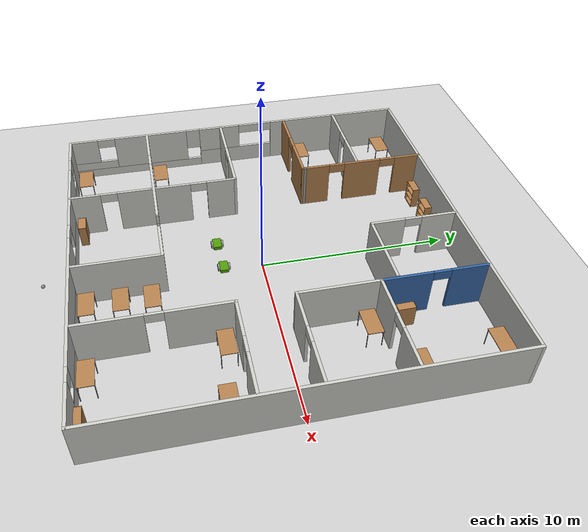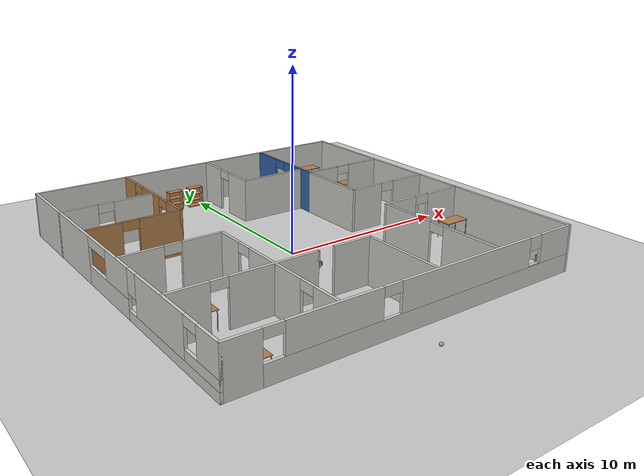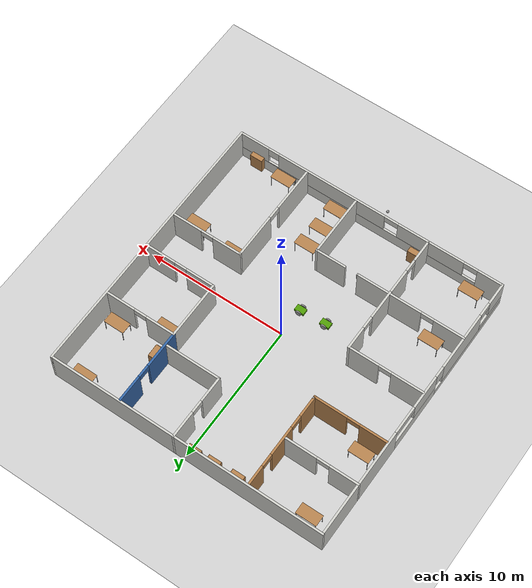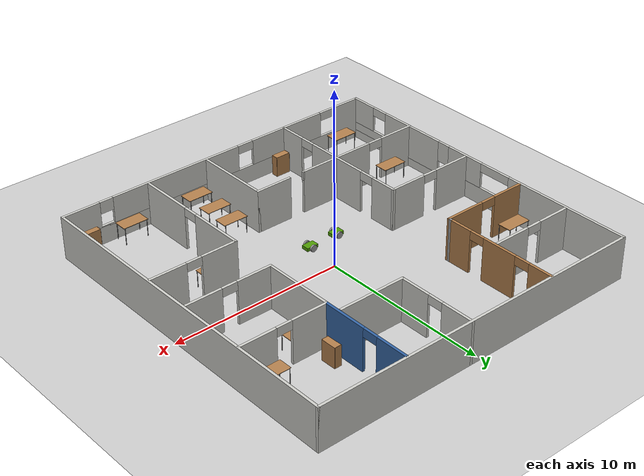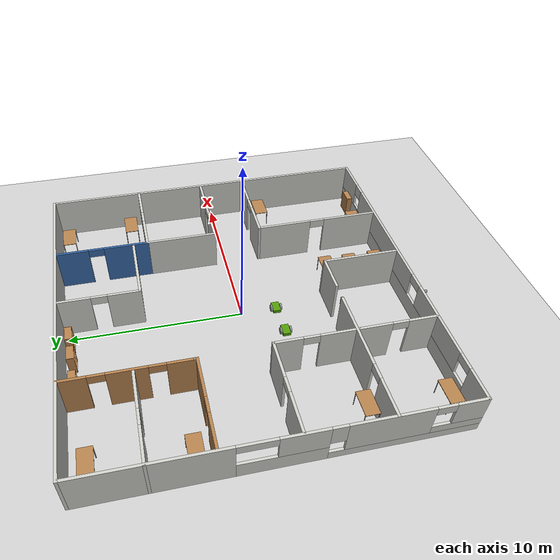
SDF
<sdf version="1.6">
 <world name="default">
  <plugin name="welcome" filename="libwelcome.so"/>
  <light name="sun" type="directional">
   <pose>0 0 10 0 -0 0</pose>
   <diffuse>0.8 0.8 0.8 1</diffuse>
   <specular>0.2 0.2 0.2 1</specular>
   <attenuation>
    <range>1000</range>
    <constant>0.9</constant>
    <linear>0.01</linear>
    <quadratic>0.001</quadratic>
   </attenuation>
   <direction>-0.5 0.1 -0.9</direction>
   <spot><inner_angle>0</inner_angle><outer_angle>0</outer_angle><falloff>0</falloff></spot>
  </light>
  <model name="ground_plane">
   <static>1</static>
   <link name="link">
    <collision name="collision">
     <geometry><plane><normal>0 0 1</normal><size>100 100</size></plane></geometry>
     <surface>
      <contact><collide_bitmask>65535</collide_bitmask></contact>
      <friction><ode><mu>100</mu><mu2>50</mu2></ode></friction>
     </surface>
    </collision>
    <visual name="visual">
     <cast_shadows>0</cast_shadows>
     <geometry><plane><normal>0 0 1</normal><size>100 100</size></plane></geometry>
     <material>
      <script><uri>file://media/materials/scripts/gazebo.material</uri><name>Gazebo/Grey</name></script>
     </material>
    </visual>
   </link>
  </model>
  <gravity>0 0 -9.8</gravity>
  <magnetic_field>6e-06 2.3e-05 -4.2e-05</magnetic_field>
  <atmosphere type="adiabatic"/>
  <physics name="default_physics" default="0" type="ode">
   <max_step_size>0.001</max_step_size>
   <real_time_factor>1</real_time_factor>
   <real_time_update_rate>1000</real_time_update_rate>
  </physics>
  <scene><ambient>0.4 0.4 0.4 1</ambient><background>0.7 0.7 0.7 1</background><shadows>1</shadows></scene>
  <spherical_coordinates>
   <surface_model>EARTH_WGS84</surface_model>
   <latitude_deg>0</latitude_deg>
   <longitude_deg>0</longitude_deg>
   <elevation>0</elevation>
   <heading_deg>0</heading_deg>
  </spherical_coordinates>
  <model name="theoffice">
   <pose>-0.089892 0.29905 0 0 -0 0</pose>
   <link name="Wall_10">
    <pose>0.001622 -9.925 0 0 -0 0</pose>
    <visual name="Wall_10_Visual_0">
     <pose>-9.06911 0 1.25 0 -0 0</pose>
     <geometry><box><size>1.86178 0.15 2.5</size></box></geometry>
     <material>
      <script><uri>file://media/materials/scripts/gazebo.material</uri><name>Gazebo/CeilingTiled</name></script>
      <ambient>0.00784314 0.00784314 0.00784314 1</ambient>
     </material>
     <meta><layer>0</layer></meta>
    </visual>
    <collision name="Wall_10_Collision_0">
     <geometry><box><size>1.86178 0.15 2.5</size></box></geometry>
     <pose>-9.06911 0 1.25 0 -0 0</pose>
    </collision>
    <visual name="Wall_10_Visual_1">
     <pose>0.930891 0 0.5 0 -0 0</pose>
     <geometry><box><size>18.1382 0.15 1</size></box></geometry>
     <material>
      <script><uri>file://media/materials/scripts/gazebo.material</uri><name>Gazebo/CeilingTiled</name></script>
      <ambient>0.00784314 0.00784314 0.00784314 1</ambient>
     </material>
     <meta><layer>0</layer></meta>
    </visual>
    <collision name="Wall_10_Collision_1">
     <geometry><box><size>18.1382 0.15 1</size></box></geometry>
     <pose>0.930891 0 0.5 0 -0 0</pose>
    </collision>
    <visual name="Wall_10_Visual_2">
     <pose>-4.6856 0 1.75 0 -0 0</pose>
     <geometry><box><size>4.90524 0.15 1.5</size></box></geometry>
     <material>
      <script><uri>file://media/materials/scripts/gazebo.material</uri><name>Gazebo/CeilingTiled</name></script>
      <ambient>0.00784314 0.00784314 0.00784314 1</ambient>
     </material>
     <meta><layer>0</layer></meta>
    </visual>
    <collision name="Wall_10_Collision_2">
     <geometry><box><size>4.90524 0.15 1.5</size></box></geometry>
     <pose>-4.6856 0 1.75 0 -0 0</pose>
    </collision>
    <visual name="Wall_10_Visual_3">
     <pose>2.85911 0 1.75 0 -0 0</pose>
     <geometry><box><size>8.18417 0.15 1.5</size></box></geometry>
     <material>
      <script><uri>file://media/materials/scripts/gazebo.material</uri><name>Gazebo/CeilingTiled</name></script>
      <ambient>0.00784314 0.00784314 0.00784314 1</ambient>
     </material>
     <meta><layer>0</layer></meta>
    </visual>
    <collision name="Wall_10_Collision_3">
     <geometry><box><size>8.18417 0.15 1.5</size></box></geometry>
     <pose>2.85911 0 1.75 0 -0 0</pose>
    </collision>
    <visual name="Wall_10_Visual_4">
     <pose>8.8756 0 1.75 0 -0 0</pose>
     <geometry><box><size>2.2488 0.15 1.5</size></box></geometry>
     <material>
      <script><uri>file://media/materials/scripts/gazebo.material</uri><name>Gazebo/CeilingTiled</name></script>
      <ambient>0.00784314 0.00784314 0.00784314 1</ambient>
     </material>
     <meta><layer>0</layer></meta>
    </visual>
    <collision name="Wall_10_Collision_4">
     <geometry><box><size>2.2488 0.15 1.5</size></box></geometry>
     <pose>8.8756 0 1.75 0 -0 0</pose>
    </collision>
    <visual name="Wall_10_Visual_5">
     <pose>7.3512 0 1 0 -0 0</pose>
     <geometry><box><size>0.8 0.15 0.1</size></box></geometry>
     <material>
      <script><uri>file://media/materials/scripts/gazebo.material</uri><name>Gazebo/CeilingTiled</name></script>
      <ambient>0.00784314 0.00784314 0.00784314 1</ambient>
     </material>
     <meta><layer>0</layer></meta>
    </visual>
    <collision name="Wall_10_Collision_5">
     <geometry><box><size>0.8 0.15 0.1</size></box></geometry>
     <pose>7.3512 0 1 0 -0 0</pose>
    </collision>
    <visual name="Wall_10_Visual_6">
     <pose>7.3512 0 2.15 0 -0 0</pose>
     <geometry><box><size>0.8 0.15 0.7</size></box></geometry>
     <material>
      <script><uri>file://media/materials/scripts/gazebo.material</uri><name>Gazebo/CeilingTiled</name></script>
      <ambient>0.00784314 0.00784314 0.00784314 1</ambient>
     </material>
     <meta><layer>0</layer></meta>
    </visual>
    <collision name="Wall_10_Collision_6">
     <geometry><box><size>0.8 0.15 0.7</size></box></geometry>
     <pose>7.3512 0 2.15 0 -0 0</pose>
    </collision>
    <visual name="Wall_10_Visual_7">
     <pose>-7.63822 0 2.25 0 -0 0</pose>
     <geometry><box><size>1 0.15 0.5</size></box></geometry>
     <material>
      <script><uri>file://media/materials/scripts/gazebo.material</uri><name>Gazebo/CeilingTiled</name></script>
      <ambient>0.00784314 0.00784314 0.00784314 1</ambient>
     </material>
     <meta><layer>0</layer></meta>
    </visual>
    <collision name="Wall_10_Collision_7">
     <geometry><box><size>1 0.15 0.5</size></box></geometry>
     <pose>-7.63822 0 2.25 0 -0 0</pose>
    </collision>
    <visual name="Wall_10_Visual_8">
     <pose>-1.73297 0 2.25 0 -0 0</pose>
     <geometry><box><size>1 0.15 0.5</size></box></geometry>
     <material>
      <script><uri>file://media/materials/scripts/gazebo.material</uri><name>Gazebo/CeilingTiled</name></script>
      <ambient>0.00784314 0.00784314 0.00784314 1</ambient>
     </material>
     <meta><layer>0</layer></meta>
    </visual>
    <collision name="Wall_10_Collision_8">
     <geometry><box><size>1 0.15 0.5</size></box></geometry>
     <pose>-1.73297 0 2.25 0 -0 0</pose>
    </collision>
   </link>
   <link name="Wall_12">
    <collision name="Wall_12_Collision">
     <geometry><box><size>20 0.15 2.5</size></box></geometry>
     <pose>0 0 1.25 0 -0 0</pose>
    </collision>
    <visual name="Wall_12_Visual">
     <pose>0 0 1.25 0 -0 0</pose>
     <geometry><box><size>20 0.15 2.5</size></box></geometry>
     <material>
      <script><uri>file://media/materials/scripts/gazebo.material</uri><name>Gazebo/CeilingTiled</name></script>
      <ambient>0.00784314 0.00784314 0.00784314 1</ambient>
     </material>
     <meta><layer>0</layer></meta>
    </visual>
    <pose>9.92662 0 0 0 -0 1.5708</pose>
   </link>
   <link name="Wall_14">
    <collision name="Wall_14_Collision">
     <geometry><box><size>20 0.15 2.5</size></box></geometry>
     <pose>0 0 1.25 0 -0 0</pose>
    </collision>
    <visual name="Wall_14_Visual">
     <pose>0 0 1.25 0 -0 0</pose>
     <geometry><box><size>20 0.15 2.5</size></box></geometry>
     <material>
      <script><uri>file://media/materials/scripts/gazebo.material</uri><name>Gazebo/CeilingTiled</name></script>
      <ambient>0.00784314 0.00784314 0.00784314 1</ambient>
     </material>
     <meta><layer>0</layer></meta>
    </visual>
    <pose>0.001622 9.925 0 0 -0 0</pose>
   </link>
   <link name="Wall_22">
    <pose>4.76809 7.15642 0 0 -0 -1.5708</pose>
    <visual name="Wall_22_Visual_0">
     <pose>-1.78497 0 1.25 0 -0 0</pose>
     <geometry><box><size>1.93005 0.15 2.5</size></box></geometry>
     <material>
      <script><uri>file://media/materials/scripts/gazebo.material</uri><name>Gazebo/Grey</name></script>
      <ambient>0.203922 0.396078 0.643137 1</ambient>
     </material>
     <meta><layer>0</layer></meta>
    </visual>
    <collision name="Wall_22_Collision_0">
     <geometry><box><size>1.93005 0.15 2.5</size></box></geometry>
     <pose>-1.78497 0 1.25 0 -0 0</pose>
    </collision>
    <visual name="Wall_22_Visual_1">
     <pose>1.41502 0 1.25 0 -0 0</pose>
     <geometry><box><size>2.66995 0.15 2.5</size></box></geometry>
     <material>
      <script><uri>file://media/materials/scripts/gazebo.material</uri><name>Gazebo/Grey</name></script>
      <ambient>0.203922 0.396078 0.643137 1</ambient>
     </material>
     <meta><layer>0</layer></meta>
    </visual>
    <collision name="Wall_22_Collision_1">
     <geometry><box><size>2.66995 0.15 2.5</size></box></geometry>
     <pose>1.41502 0 1.25 0 -0 0</pose>
    </collision>
    <visual name="Wall_22_Visual_2">
     <pose>-0.36995 0 2.25 0 -0 0</pose>
     <geometry><box><size>0.9 0.15 0.5</size></box></geometry>
     <material>
      <script><uri>file://media/materials/scripts/gazebo.material</uri><name>Gazebo/Grey</name></script>
      <ambient>0.203922 0.396078 0.643137 1</ambient>
     </material>
     <meta><layer>0</layer></meta>
    </visual>
    <collision name="Wall_22_Collision_2">
     <geometry><box><size>0.9 0.15 0.5</size></box></geometry>
     <pose>-0.36995 0 2.25 0 -0 0</pose>
    </collision>
   </link>
   <link name="Wall_25">
    <pose>7.31809 4.48142 0 0 -0 0</pose>
    <visual name="Wall_25_Visual_0">
     <pose>-1.54018 0 1.25 0 -0 0</pose>
     <geometry><box><size>2.16963 0.15 2.5</size></box></geometry>
     <material>
      <script><uri>file://media/materials/scripts/gazebo.material</uri><name>Gazebo/CeilingTiled</name></script>
      <ambient>0.203922 0.396078 0.643137 1</ambient>
     </material>
     <meta><layer>0</layer></meta>
    </visual>
    <collision name="Wall_25_Collision_0">
     <geometry><box><size>2.16963 0.15 2.5</size></box></geometry>
     <pose>-1.54018 0 1.25 0 -0 0</pose>
    </collision>
    <visual name="Wall_25_Visual_1">
     <pose>1.53482 0 1.25 0 -0 0</pose>
     <geometry><box><size>2.18037 0.15 2.5</size></box></geometry>
     <material>
      <script><uri>file://media/materials/scripts/gazebo.material</uri><name>Gazebo/CeilingTiled</name></script>
      <ambient>0.203922 0.396078 0.643137 1</ambient>
     </material>
     <meta><layer>0</layer></meta>
    </visual>
    <collision name="Wall_25_Collision_1">
     <geometry><box><size>2.18037 0.15 2.5</size></box></geometry>
     <pose>1.53482 0 1.25 0 -0 0</pose>
    </collision>
    <visual name="Wall_25_Visual_2">
     <pose>-0.00537 0 2.25 0 -0 0</pose>
     <geometry><box><size>0.9 0.15 0.5</size></box></geometry>
     <material>
      <script><uri>file://media/materials/scripts/gazebo.material</uri><name>Gazebo/CeilingTiled</name></script>
      <ambient>0.203922 0.396078 0.643137 1</ambient>
     </material>
     <meta><layer>0</layer></meta>
    </visual>
    <collision name="Wall_25_Collision_2">
     <geometry><box><size>0.9 0.15 0.5</size></box></geometry>
     <pose>-0.00537 0 2.25 0 -0 0</pose>
    </collision>
   </link>
   <link name="Wall_30">
    <pose>-4.49838 -5.4215 0 0 -0 0</pose>
    <visual name="Wall_30_Visual_0">
     <pose>-4.37611 0 1.25 0 -0 0</pose>
     <geometry><box><size>2.24779 0.15 2.5</size></box></geometry>
     <material>
      <script><uri>file://media/materials/scripts/gazebo.material</uri><name>Gazebo/CeilingTiled</name></script>
      <ambient>0.988235 0.913725 0.309804 1</ambient>
     </material>
     <meta><layer>0</layer></meta>
    </visual>
    <collision name="Wall_30_Collision_0">
     <geometry><box><size>2.24779 0.15 2.5</size></box></geometry>
     <pose>-4.37611 0 1.25 0 -0 0</pose>
    </collision>
    <visual name="Wall_30_Visual_1">
     <pose>0.005075 0 1.25 0 -0 0</pose>
     <geometry><box><size>4.71457 0.15 2.5</size></box></geometry>
     <material>
      <script><uri>file://media/materials/scripts/gazebo.material</uri><name>Gazebo/CeilingTiled</name></script>
      <ambient>0.988235 0.913725 0.309804 1</ambient>
     </material>
     <meta><layer>0</layer></meta>
    </visual>
    <collision name="Wall_30_Collision_1">
     <geometry><box><size>4.71457 0.15 2.5</size></box></geometry>
     <pose>0.005075 0 1.25 0 -0 0</pose>
    </collision>
    <visual name="Wall_30_Visual_2">
     <pose>4.38118 0 1.25 0 -0 0</pose>
     <geometry><box><size>2.23764 0.15 2.5</size></box></geometry>
     <material>
      <script><uri>file://media/materials/scripts/gazebo.material</uri><name>Gazebo/CeilingTiled</name></script>
      <ambient>0.988235 0.913725 0.309804 1</ambient>
     </material>
     <meta><layer>0</layer></meta>
    </visual>
    <collision name="Wall_30_Collision_2">
     <geometry><box><size>2.23764 0.15 2.5</size></box></geometry>
     <pose>4.38118 0 1.25 0 -0 0</pose>
    </collision>
    <visual name="Wall_30_Visual_3">
     <pose>-2.80221 0 2.25 0 -0 0</pose>
     <geometry><box><size>0.9 0.15 0.5</size></box></geometry>
     <material>
      <script><uri>file://media/materials/scripts/gazebo.material</uri><name>Gazebo/CeilingTiled</name></script>
      <ambient>0.988235 0.913725 0.309804 1</ambient>
     </material>
     <meta><layer>0</layer></meta>
    </visual>
    <collision name="Wall_30_Collision_3">
     <geometry><box><size>0.9 0.15 0.5</size></box></geometry>
     <pose>-2.80221 0 2.25 0 -0 0</pose>
    </collision>
    <visual name="Wall_30_Visual_4">
     <pose>2.36236 0 2.25 0 -0 0</pose>
     <geometry><box><size>0.1 0.15 0.5</size></box></geometry>
     <material>
      <script><uri>file://media/materials/scripts/gazebo.material</uri><name>Gazebo/CeilingTiled</name></script>
      <ambient>0.988235 0.913725 0.309804 1</ambient>
     </material>
     <meta><layer>0</layer></meta>
    </visual>
    <collision name="Wall_30_Collision_4">
     <geometry><box><size>0.1 0.15 0.5</size></box></geometry>
     <pose>2.36236 0 2.25 0 -0 0</pose>
    </collision>
   </link>
   <link name="Wall_31">
    <collision name="Wall_31_Collision">
     <geometry><box><size>4.5 0.15 2.5</size></box></geometry>
     <pose>0 0 1.25 0 -0 0</pose>
    </collision>
    <visual name="Wall_31_Visual">
     <pose>0 0 1.25 0 -0 0</pose>
     <geometry><box><size>4.5 0.15 2.5</size></box></geometry>
     <material>
      <script><uri>file://media/materials/scripts/gazebo.material</uri><name>Gazebo/CeilingTiled</name></script>
      <ambient>0.988235 0.913725 0.309804 1</ambient>
     </material>
     <meta><layer>0</layer></meta>
    </visual>
    <pose>0.926622 -7.5965 0 0 -0 -1.5708</pose>
   </link>
   <link name="Wall_33">
    <pose>-4.49596 -7.69007 0 0 -0 -1.5708</pose>
    <visual name="Wall_33_Visual_0">
     <pose>-1.27394 0 1.25 0 -0 0</pose>
     <geometry><box><size>1.95211 0.15 2.5</size></box></geometry>
     <material>
      <script><uri>file://media/materials/scripts/gazebo.material</uri><name>Gazebo/CeilingTiled</name></script>
      <ambient>0.203922 0.396078 0.643137 1</ambient>
     </material>
     <meta><layer>0</layer></meta>
    </visual>
    <collision name="Wall_33_Collision_0">
     <geometry><box><size>1.95211 0.15 2.5</size></box></geometry>
     <pose>-1.27394 0 1.25 0 -0 0</pose>
    </collision>
    <visual name="Wall_33_Visual_1">
     <pose>1.42606 0 1.25 0 -0 0</pose>
     <geometry><box><size>1.64789 0.15 2.5</size></box></geometry>
     <material>
      <script><uri>file://media/materials/scripts/gazebo.material</uri><name>Gazebo/CeilingTiled</name></script>
      <ambient>0.203922 0.396078 0.643137 1</ambient>
     </material>
     <meta><layer>0</layer></meta>
    </visual>
    <collision name="Wall_33_Collision_1">
     <geometry><box><size>1.64789 0.15 2.5</size></box></geometry>
     <pose>1.42606 0 1.25 0 -0 0</pose>
    </collision>
    <visual name="Wall_33_Visual_2">
     <pose>0.152112 0 2.25 0 -0 0</pose>
     <geometry><box><size>0.9 0.15 0.5</size></box></geometry>
     <material>
      <script><uri>file://media/materials/scripts/gazebo.material</uri><name>Gazebo/CeilingTiled</name></script>
      <ambient>0.203922 0.396078 0.643137 1</ambient>
     </material>
     <meta><layer>0</layer></meta>
    </visual>
    <collision name="Wall_33_Collision_2">
     <geometry><box><size>0.9 0.15 0.5</size></box></geometry>
     <pose>0.152112 0 2.25 0 -0 0</pose>
    </collision>
   </link>
   <link name="Wall_35">
    <collision name="Wall_35_Collision">
     <geometry><box><size>4.25 0.15 2.5</size></box></geometry>
     <pose>0 0 1.25 0 -0 0</pose>
    </collision>
    <visual name="Wall_35_Visual">
     <pose>0 0 1.25 0 -0 0</pose>
     <geometry><box><size>4.25 0.15 2.5</size></box></geometry>
     <material>
      <script><uri>file://media/materials/scripts/gazebo.material</uri><name>Gazebo/CeilingTiled</name></script>
      <ambient>0.988235 0.913725 0.309804 1</ambient>
     </material>
     <meta><layer>0</layer></meta>
    </visual>
    <pose>4.76809 2.43142 0 0 -0 -1.5708</pose>
   </link>
   <link name="Wall_36">
    <pose>7.31809 0.381424 0 0 -0 0</pose>
    <visual name="Wall_36_Visual_0">
     <pose>-1.56417 0 1.25 0 -0 0</pose>
     <geometry><box><size>2.12167 0.15 2.5</size></box></geometry>
     <material>
      <script><uri>file://media/materials/scripts/gazebo.material</uri><name>Gazebo/CeilingTiled</name></script>
      <ambient>0.180392 0.203922 0.211765 1</ambient>
     </material>
     <meta><layer>0</layer></meta>
    </visual>
    <collision name="Wall_36_Collision_0">
     <geometry><box><size>2.12167 0.15 2.5</size></box></geometry>
     <pose>-1.56417 0 1.25 0 -0 0</pose>
    </collision>
    <visual name="Wall_36_Visual_1">
     <pose>1.51083 0 1.25 0 -0 0</pose>
     <geometry><box><size>2.22833 0.15 2.5</size></box></geometry>
     <material>
      <script><uri>file://media/materials/scripts/gazebo.material</uri><name>Gazebo/CeilingTiled</name></script>
      <ambient>0.180392 0.203922 0.211765 1</ambient>
     </material>
     <meta><layer>0</layer></meta>
    </visual>
    <collision name="Wall_36_Collision_1">
     <geometry><box><size>2.22833 0.15 2.5</size></box></geometry>
     <pose>1.51083 0 1.25 0 -0 0</pose>
    </collision>
    <visual name="Wall_36_Visual_2">
     <pose>-0.053335 0 2.25 0 -0 0</pose>
     <geometry><box><size>0.9 0.15 0.5</size></box></geometry>
     <material>
      <script><uri>file://media/materials/scripts/gazebo.material</uri><name>Gazebo/CeilingTiled</name></script>
      <ambient>0.180392 0.203922 0.211765 1</ambient>
     </material>
     <meta><layer>0</layer></meta>
    </visual>
    <collision name="Wall_36_Collision_2">
     <geometry><box><size>0.9 0.15 0.5</size></box></geometry>
     <pose>-0.053335 0 2.25 0 -0 0</pose>
    </collision>
   </link>
   <link name="Wall_38">
    <pose>7.2712 -2.42706 0 0 -0 3.14159</pose>
    <visual name="Wall_38_Visual_0">
     <pose>-1.53166 0 1.25 0 -0 0</pose>
     <geometry><box><size>2.18669 0.15 2.5</size></box></geometry>
     <material>
      <script><uri>file://media/materials/scripts/gazebo.material</uri><name>Gazebo/CeilingTiled</name></script>
      <ambient>0.988235 0.913725 0.309804 1</ambient>
     </material>
     <meta><layer>0</layer></meta>
    </visual>
    <collision name="Wall_38_Collision_0">
     <geometry><box><size>2.18669 0.15 2.5</size></box></geometry>
     <pose>-1.53166 0 1.25 0 -0 0</pose>
    </collision>
    <visual name="Wall_38_Visual_1">
     <pose>1.54334 0 1.25 0 -0 0</pose>
     <geometry><box><size>2.16331 0.15 2.5</size></box></geometry>
     <material>
      <script><uri>file://media/materials/scripts/gazebo.material</uri><name>Gazebo/CeilingTiled</name></script>
      <ambient>0.988235 0.913725 0.309804 1</ambient>
     </material>
     <meta><layer>0</layer></meta>
    </visual>
    <collision name="Wall_38_Collision_1">
     <geometry><box><size>2.16331 0.15 2.5</size></box></geometry>
     <pose>1.54334 0 1.25 0 -0 0</pose>
    </collision>
    <visual name="Wall_38_Visual_2">
     <pose>0.011685 0 2.25 0 -0 0</pose>
     <geometry><box><size>0.9 0.15 0.5</size></box></geometry>
     <material>
      <script><uri>file://media/materials/scripts/gazebo.material</uri><name>Gazebo/CeilingTiled</name></script>
      <ambient>0.988235 0.913725 0.309804 1</ambient>
     </material>
     <meta><layer>0</layer></meta>
    </visual>
    <collision name="Wall_38_Collision_2">
     <geometry><box><size>0.9 0.15 0.5</size></box></geometry>
     <pose>0.011685 0 2.25 0 -0 0</pose>
    </collision>
   </link>
   <link name="Wall_39">
    <pose>4.7212 -6.10206 0 0 -0 -1.5708</pose>
    <visual name="Wall_39_Visual_0">
     <pose>-2.08433 0 1.25 0 -0 0</pose>
     <geometry><box><size>3.33134 0.15 2.5</size></box></geometry>
     <material>
      <script><uri>file://media/materials/scripts/gazebo.material</uri><name>Gazebo/CeilingTiled</name></script>
      <ambient>0.988235 0.913725 0.309804 1</ambient>
     </material>
     <meta><layer>0</layer></meta>
    </visual>
    <collision name="Wall_39_Collision_0">
     <geometry><box><size>3.33134 0.15 2.5</size></box></geometry>
     <pose>-2.08433 0 1.25 0 -0 0</pose>
    </collision>
    <visual name="Wall_39_Visual_1">
     <pose>2.11567 0 1.25 0 -0 0</pose>
     <geometry><box><size>3.26866 0.15 2.5</size></box></geometry>
     <material>
      <script><uri>file://media/materials/scripts/gazebo.material</uri><name>Gazebo/CeilingTiled</name></script>
      <ambient>0.988235 0.913725 0.309804 1</ambient>
     </material>
     <meta><layer>0</layer></meta>
    </visual>
    <collision name="Wall_39_Collision_1">
     <geometry><box><size>3.26866 0.15 2.5</size></box></geometry>
     <pose>2.11567 0 1.25 0 -0 0</pose>
    </collision>
    <visual name="Wall_39_Visual_2">
     <pose>0.031344 0 2.25 0 -0 0</pose>
     <geometry><box><size>0.9 0.15 0.5</size></box></geometry>
     <material>
      <script><uri>file://media/materials/scripts/gazebo.material</uri><name>Gazebo/CeilingTiled</name></script>
      <ambient>0.988235 0.913725 0.309804 1</ambient>
     </material>
     <meta><layer>0</layer></meta>
    </visual>
    <collision name="Wall_39_Collision_2">
     <geometry><box><size>0.9 0.15 0.5</size></box></geometry>
     <pose>0.031344 0 2.25 0 -0 0</pose>
    </collision>
   </link>
   <link name="Wall_41">
    <pose>-4.49596 -3.21507 0 0 -0 1.5708</pose>
    <visual name="Wall_41_Visual_0">
     <pose>-1.28494 0 1.25 0 -0 0</pose>
     <geometry><box><size>2.18012 0.15 2.5</size></box></geometry>
     <material>
      <script><uri>file://media/materials/scripts/gazebo.material</uri><name>Gazebo/CeilingTiled</name></script>
      <ambient>0.203922 0.396078 0.643137 1</ambient>
     </material>
     <meta><layer>0</layer></meta>
    </visual>
    <collision name="Wall_41_Collision_0">
     <geometry><box><size>2.18012 0.15 2.5</size></box></geometry>
     <pose>-1.28494 0 1.25 0 -0 0</pose>
    </collision>
    <visual name="Wall_41_Visual_1">
     <pose>1.54006 0 1.25 0 -0 0</pose>
     <geometry><box><size>1.66987 0.15 2.5</size></box></geometry>
     <material>
      <script><uri>file://media/materials/scripts/gazebo.material</uri><name>Gazebo/CeilingTiled</name></script>
      <ambient>0.203922 0.396078 0.643137 1</ambient>
     </material>
     <meta><layer>0</layer></meta>
    </visual>
    <collision name="Wall_41_Collision_1">
     <geometry><box><size>1.66987 0.15 2.5</size></box></geometry>
     <pose>1.54006 0 1.25 0 -0 0</pose>
    </collision>
    <visual name="Wall_41_Visual_2">
     <pose>0.255125 0 2.25 0 -0 0</pose>
     <geometry><box><size>0.9 0.15 0.5</size></box></geometry>
     <material>
      <script><uri>file://media/materials/scripts/gazebo.material</uri><name>Gazebo/CeilingTiled</name></script>
      <ambient>0.203922 0.396078 0.643137 1</ambient>
     </material>
     <meta><layer>0</layer></meta>
    </visual>
    <collision name="Wall_41_Collision_2">
     <geometry><box><size>0.9 0.15 0.5</size></box></geometry>
     <pose>0.255125 0 2.25 0 -0 0</pose>
    </collision>
   </link>
   <link name="Wall_44">
    <pose>-7.17096 -0.915074 0 0 -0 3.14159</pose>
    <visual name="Wall_44_Visual_0">
     <pose>-1.61655 0 1.25 0 -0 0</pose>
     <geometry><box><size>2.26689 0.15 2.5</size></box></geometry>
     <material>
      <script><uri>file://media/materials/scripts/gazebo.material</uri><name>Gazebo/CeilingTiled</name></script>
      <ambient>0.988235 0.913725 0.309804 1</ambient>
     </material>
     <meta><layer>0</layer></meta>
    </visual>
    <collision name="Wall_44_Collision_0">
     <geometry><box><size>2.26689 0.15 2.5</size></box></geometry>
     <pose>-1.61655 0 1.25 0 -0 0</pose>
    </collision>
    <visual name="Wall_44_Visual_1">
     <pose>1.58344 0 1.25 0 -0 0</pose>
     <geometry><box><size>2.33311 0.15 2.5</size></box></geometry>
     <material>
      <script><uri>file://media/materials/scripts/gazebo.material</uri><name>Gazebo/CeilingTiled</name></script>
      <ambient>0.988235 0.913725 0.309804 1</ambient>
     </material>
     <meta><layer>0</layer></meta>
    </visual>
    <collision name="Wall_44_Collision_1">
     <geometry><box><size>2.33311 0.15 2.5</size></box></geometry>
     <pose>1.58344 0 1.25 0 -0 0</pose>
    </collision>
    <visual name="Wall_44_Visual_2">
     <pose>-0.033111 0 2.25 0 -0 0</pose>
     <geometry><box><size>0.9 0.15 0.5</size></box></geometry>
     <material>
      <script><uri>file://media/materials/scripts/gazebo.material</uri><name>Gazebo/CeilingTiled</name></script>
      <ambient>0.988235 0.913725 0.309804 1</ambient>
     </material>
     <meta><layer>0</layer></meta>
    </visual>
    <collision name="Wall_44_Collision_2">
     <geometry><box><size>0.9 0.15 0.5</size></box></geometry>
     <pose>-0.033111 0 2.25 0 -0 0</pose>
    </collision>
   </link>
   <link name="Wall_47">
    <pose>0.74431 7.625 0 0 -0 -1.5708</pose>
    <visual name="Wall_47_Visual_0">
     <pose>-1.38979 0 1.25 0 -0 0</pose>
     <geometry><box><size>1.97043 0.15 2.5</size></box></geometry>
     <material>
      <script><uri>file://media/materials/scripts/gazebo.material</uri><name>Gazebo/CeilingTiled</name></script>
      <ambient>0.988235 0.913725 0.309804 1</ambient>
     </material>
     <meta><layer>0</layer></meta>
    </visual>
    <collision name="Wall_47_Collision_0">
     <geometry><box><size>1.97043 0.15 2.5</size></box></geometry>
     <pose>-1.38979 0 1.25 0 -0 0</pose>
    </collision>
    <visual name="Wall_47_Visual_1">
     <pose>1.43521 0 1.25 0 -0 0</pose>
     <geometry><box><size>1.87957 0.15 2.5</size></box></geometry>
     <material>
      <script><uri>file://media/materials/scripts/gazebo.material</uri><name>Gazebo/CeilingTiled</name></script>
      <ambient>0.988235 0.913725 0.309804 1</ambient>
     </material>
     <meta><layer>0</layer></meta>
    </visual>
    <collision name="Wall_47_Collision_1">
     <geometry><box><size>1.87957 0.15 2.5</size></box></geometry>
     <pose>1.43521 0 1.25 0 -0 0</pose>
    </collision>
    <visual name="Wall_47_Visual_2">
     <pose>0.045426 0 2.25 0 -0 0</pose>
     <geometry><box><size>0.9 0.15 0.5</size></box></geometry>
     <material>
      <script><uri>file://media/materials/scripts/gazebo.material</uri><name>Gazebo/CeilingTiled</name></script>
      <ambient>0.988235 0.913725 0.309804 1</ambient>
     </material>
     <meta><layer>0</layer></meta>
    </visual>
    <collision name="Wall_47_Collision_2">
     <geometry><box><size>0.9 0.15 0.5</size></box></geometry>
     <pose>0.045426 0 2.25 0 -0 0</pose>
    </collision>
   </link>
   <link name="Wall_48">
    <collision name="Wall_48_Collision">
     <geometry><box><size>4 0.15 2.5</size></box></geometry>
     <pose>0 0 1.25 0 -0 0</pose>
    </collision>
    <visual name="Wall_48_Visual">
     <pose>0 0 1.25 0 -0 0</pose>
     <geometry><box><size>4 0.15 2.5</size></box></geometry>
     <material>
      <script><uri>file://media/materials/scripts/gazebo.material</uri><name>Gazebo/CeilingTiled</name></script>
      <ambient>0.988235 0.913725 0.309804 1</ambient>
     </material>
     <meta><layer>0</layer></meta>
    </visual>
    <pose>2.66931 5.325 0 0 -0 0</pose>
   </link>
   <link name="Wall_50">
    <pose>-7.24167 3.02777 0 0 -0 0</pose>
    <visual name="Wall_50_Visual_0">
     <pose>-1.66058 0 1.25 0 -0 0</pose>
     <geometry><box><size>1.97784 0.15 2.5</size></box></geometry>
     <material>
      <script><uri>file://media/materials/scripts/gazebo.material</uri><name>Gazebo/Wood</name></script>
      <ambient>1 1 1 1</ambient>
     </material>
     <meta><layer>0</layer></meta>
    </visual>
    <collision name="Wall_50_Collision_0">
     <geometry><box><size>1.97784 0.15 2.5</size></box></geometry>
     <pose>-1.66058 0 1.25 0 -0 0</pose>
    </collision>
    <visual name="Wall_50_Visual_1">
     <pose>1.43892 0 1.25 0 -0 0</pose>
     <geometry><box><size>2.42116 0.15 2.5</size></box></geometry>
     <material>
      <script><uri>file://media/materials/scripts/gazebo.material</uri><name>Gazebo/Wood</name></script>
      <ambient>1 1 1 1</ambient>
     </material>
     <meta><layer>0</layer></meta>
    </visual>
    <collision name="Wall_50_Collision_1">
     <geometry><box><size>2.42116 0.15 2.5</size></box></geometry>
     <pose>1.43892 0 1.25 0 -0 0</pose>
    </collision>
    <visual name="Wall_50_Visual_2">
     <pose>-0.221664 0 2.25 0 -0 0</pose>
     <geometry><box><size>0.9 0.15 0.5</size></box></geometry>
     <material>
      <script><uri>file://media/materials/scripts/gazebo.material</uri><name>Gazebo/Wood</name></script>
      <ambient>1 1 1 1</ambient>
     </material>
     <meta><layer>0</layer></meta>
    </visual>
    <collision name="Wall_50_Collision_2">
     <geometry><box><size>0.9 0.15 0.5</size></box></geometry>
     <pose>-0.221664 0 2.25 0 -0 0</pose>
    </collision>
   </link>
   <link name="Wall_55">
    <collision name="Wall_55_Collision">
     <geometry><box><size>0.15 0.15 2.5</size></box></geometry>
     <pose>0 0 1.25 0 -0 0</pose>
    </collision>
    <visual name="Wall_55_Visual">
     <pose>0 0 1.25 0 -0 0</pose>
     <geometry><box><size>0.15 0.15 2.5</size></box></geometry>
     <material>
      <script><uri>file://media/materials/scripts/gazebo.material</uri><name>Gazebo/Grey</name></script>
      <ambient>1 1 1 1</ambient>
     </material>
     <meta><layer>0</layer></meta>
    </visual>
    <pose>-4.66695 3.1448 0 0 -0 0</pose>
   </link>
   <link name="Wall_58">
    <pose>-4.66717 6.45277 0 0 -0 1.5708</pose>
    <visual name="Wall_58_Visual_0">
     <pose>-2.6942 0 1.25 0 -0 0</pose>
     <geometry><box><size>1.6116 0.15 2.5</size></box></geometry>
     <material>
      <script><uri>file://media/materials/scripts/gazebo.material</uri><name>Gazebo/Wood</name></script>
      <ambient>1 1 1 1</ambient>
     </material>
     <meta><layer>0</layer></meta>
    </visual>
    <collision name="Wall_58_Collision_0">
     <geometry><box><size>1.6116 0.15 2.5</size></box></geometry>
     <pose>-2.6942 0 1.25 0 -0 0</pose>
    </collision>
    <visual name="Wall_58_Visual_1">
     <pose>0.066958 0 1.25 0 -0 0</pose>
     <geometry><box><size>2.11071 0.15 2.5</size></box></geometry>
     <material>
      <script><uri>file://media/materials/scripts/gazebo.material</uri><name>Gazebo/Wood</name></script>
      <ambient>1 1 1 1</ambient>
     </material>
     <meta><layer>0</layer></meta>
    </visual>
    <collision name="Wall_58_Collision_1">
     <geometry><box><size>2.11071 0.15 2.5</size></box></geometry>
     <pose>0.066958 0 1.25 0 -0 0</pose>
    </collision>
    <visual name="Wall_58_Visual_2">
     <pose>2.76116 0 1.25 0 -0 0</pose>
     <geometry><box><size>1.47769 0.15 2.5</size></box></geometry>
     <material>
      <script><uri>file://media/materials/scripts/gazebo.material</uri><name>Gazebo/Wood</name></script>
      <ambient>1 1 1 1</ambient>
     </material>
     <meta><layer>0</layer></meta>
    </visual>
    <collision name="Wall_58_Collision_2">
     <geometry><box><size>1.47769 0.15 2.5</size></box></geometry>
     <pose>2.76116 0 1.25 0 -0 0</pose>
    </collision>
    <visual name="Wall_58_Visual_3">
     <pose>-1.4384 0 2.25 0 -0 0</pose>
     <geometry><box><size>0.9 0.15 0.5</size></box></geometry>
     <material>
      <script><uri>file://media/materials/scripts/gazebo.material</uri><name>Gazebo/Wood</name></script>
      <ambient>1 1 1 1</ambient>
     </material>
     <meta><layer>0</layer></meta>
    </visual>
    <collision name="Wall_58_Collision_3">
     <geometry><box><size>0.9 0.15 0.5</size></box></geometry>
     <pose>-1.4384 0 2.25 0 -0 0</pose>
    </collision>
    <visual name="Wall_58_Visual_4">
     <pose>1.57231 0 2.25 0 -0 0</pose>
     <geometry><box><size>0.9 0.15 0.5</size></box></geometry>
     <material>
      <script><uri>file://media/materials/scripts/gazebo.material</uri><name>Gazebo/Wood</name></script>
      <ambient>1 1 1 1</ambient>
     </material>
     <meta><layer>0</layer></meta>
    </visual>
    <collision name="Wall_58_Collision_4">
     <geometry><box><size>0.9 0.15 0.5</size></box></geometry>
     <pose>1.57231 0 2.25 0 -0 0</pose>
    </collision>
   </link>
   <link name="Wall_60">
    <pose>-7.37662 6.21928 0 0 -0 0</pose>
    <visual name="Wall_60_Visual_0">
     <pose>-1.57496 0 1.25 0 -0 0</pose>
     <geometry><box><size>2.10009 0.15 2.5</size></box></geometry>
     <material>
      <script><uri>file://media/materials/scripts/gazebo.material</uri><name>Gazebo/CeilingTiled</name></script>
      <ambient>0.203922 0.396078 0.643137 1</ambient>
     </material>
     <meta><layer>0</layer></meta>
    </visual>
    <collision name="Wall_60_Collision_0">
     <geometry><box><size>2.10009 0.15 2.5</size></box></geometry>
     <pose>-1.57496 0 1.25 0 -0 0</pose>
    </collision>
    <visual name="Wall_60_Visual_1">
     <pose>1.50005 0 1.25 0 -0 0</pose>
     <geometry><box><size>2.24991 0.15 2.5</size></box></geometry>
     <material>
      <script><uri>file://media/materials/scripts/gazebo.material</uri><name>Gazebo/CeilingTiled</name></script>
      <ambient>0.203922 0.396078 0.643137 1</ambient>
     </material>
     <meta><layer>0</layer></meta>
    </visual>
    <collision name="Wall_60_Collision_1">
     <geometry><box><size>2.24991 0.15 2.5</size></box></geometry>
     <pose>1.50005 0 1.25 0 -0 0</pose>
    </collision>
    <visual name="Wall_60_Visual_2">
     <pose>-0.074909 0 2.25 0 -0 0</pose>
     <geometry><box><size>0.9 0.15 0.5</size></box></geometry>
     <material>
      <script><uri>file://media/materials/scripts/gazebo.material</uri><name>Gazebo/CeilingTiled</name></script>
      <ambient>0.203922 0.396078 0.643137 1</ambient>
     </material>
     <meta><layer>0</layer></meta>
    </visual>
    <collision name="Wall_60_Collision_2">
     <geometry><box><size>0.9 0.15 0.5</size></box></geometry>
     <pose>-0.074909 0 2.25 0 -0 0</pose>
    </collision>
   </link>
   <link name="Wall_7">
    <pose>-9.92338 0 0 0 -0 -1.5708</pose>
    <visual name="Wall_7_Visual_0">
     <pose>-6.10882 0 1.25 0 -0 0</pose>
     <geometry><box><size>7.78235 0.15 2.5</size></box></geometry>
     <material>
      <script><uri>file://media/materials/scripts/gazebo.material</uri><name>Gazebo/CeilingTiled</name></script>
      <ambient>0.00784314 0.00784314 0.00784314 1</ambient>
     </material>
     <meta><layer>0</layer></meta>
    </visual>
    <collision name="Wall_7_Collision_0">
     <geometry><box><size>7.78235 0.15 2.5</size></box></geometry>
     <pose>-6.10882 0 1.25 0 -0 0</pose>
    </collision>
    <visual name="Wall_7_Visual_1">
     <pose>0.008628 0 0.5 0 -0 0</pose>
     <geometry><box><size>4.45255 0.15 1</size></box></geometry>
     <material>
      <script><uri>file://media/materials/scripts/gazebo.material</uri><name>Gazebo/CeilingTiled</name></script>
      <ambient>0.00784314 0.00784314 0.00784314 1</ambient>
     </material>
     <meta><layer>0</layer></meta>
    </visual>
    <collision name="Wall_7_Collision_1">
     <geometry><box><size>4.45255 0.15 1</size></box></geometry>
     <pose>0.008628 0 0.5 0 -0 0</pose>
    </collision>
    <visual name="Wall_7_Visual_2">
     <pose>6.11745 0 0.25 0 -0 0</pose>
     <geometry><box><size>7.7651 0.15 0.5</size></box></geometry>
     <material>
      <script><uri>file://media/materials/scripts/gazebo.material</uri><name>Gazebo/CeilingTiled</name></script>
      <ambient>0.00784314 0.00784314 0.00784314 1</ambient>
     </material>
     <meta><layer>0</layer></meta>
    </visual>
    <collision name="Wall_7_Collision_2">
     <geometry><box><size>7.7651 0.15 0.5</size></box></geometry>
     <pose>6.11745 0 0.25 0 -0 0</pose>
    </collision>
    <visual name="Wall_7_Visual_3">
     <pose>5.19172 0 1.5 0 -0 0</pose>
     <geometry><box><size>4.31364 0.15 2</size></box></geometry>
     <material>
      <script><uri>file://media/materials/scripts/gazebo.material</uri><name>Gazebo/CeilingTiled</name></script>
      <ambient>0.00784314 0.00784314 0.00784314 1</ambient>
     </material>
     <meta><layer>0</layer></meta>
    </visual>
    <collision name="Wall_7_Collision_3">
     <geometry><box><size>4.31364 0.15 2</size></box></geometry>
     <pose>5.19172 0 1.5 0 -0 0</pose>
    </collision>
    <visual name="Wall_7_Visual_4">
     <pose>8.67427 0 0.75 0 -0 0</pose>
     <geometry><box><size>2.65146 0.15 0.5</size></box></geometry>
     <material>
      <script><uri>file://media/materials/scripts/gazebo.material</uri><name>Gazebo/CeilingTiled</name></script>
      <ambient>0.00784314 0.00784314 0.00784314 1</ambient>
     </material>
     <meta><layer>0</layer></meta>
    </visual>
    <collision name="Wall_7_Collision_4">
     <geometry><box><size>2.65146 0.15 0.5</size></box></geometry>
     <pose>8.67427 0 0.75 0 -0 0</pose>
    </collision>
    <visual name="Wall_7_Visual_5">
     <pose>1.00863 0 1.75 0 -0 0</pose>
     <geometry><box><size>2.45255 0.15 1.5</size></box></geometry>
     <material>
      <script><uri>file://media/materials/scripts/gazebo.material</uri><name>Gazebo/CeilingTiled</name></script>
      <ambient>0.00784314 0.00784314 0.00784314 1</ambient>
     </material>
     <meta><layer>0</layer></meta>
    </visual>
    <collision name="Wall_7_Collision_5">
     <geometry><box><size>2.45255 0.15 1.5</size></box></geometry>
     <pose>1.00863 0 1.75 0 -0 0</pose>
    </collision>
    <visual name="Wall_7_Visual_6">
     <pose>1.00863 0 1.75 0 -0 0</pose>
     <geometry><box><size>2.45255 0.15 1.5</size></box></geometry>
     <material>
      <script><uri>file://media/materials/scripts/gazebo.material</uri><name>Gazebo/CeilingTiled</name></script>
      <ambient>0.00784314 0.00784314 0.00784314 1</ambient>
     </material>
     <meta><layer>0</layer></meta>
    </visual>
    <collision name="Wall_7_Collision_6">
     <geometry><box><size>2.45255 0.15 1.5</size></box></geometry>
     <pose>1.00863 0 1.75 0 -0 0</pose>
    </collision>
    <visual name="Wall_7_Visual_7">
     <pose>9.17427 0 1.75 0 -0 0</pose>
     <geometry><box><size>1.65146 0.15 1.5</size></box></geometry>
     <material>
      <script><uri>file://media/materials/scripts/gazebo.material</uri><name>Gazebo/CeilingTiled</name></script>
      <ambient>0.00784314 0.00784314 0.00784314 1</ambient>
     </material>
     <meta><layer>0</layer></meta>
    </visual>
    <collision name="Wall_7_Collision_7">
     <geometry><box><size>1.65146 0.15 1.5</size></box></geometry>
     <pose>9.17427 0 1.75 0 -0 0</pose>
    </collision>
    <visual name="Wall_7_Visual_8">
     <pose>2.6349 0 1.9 0 -0 0</pose>
     <geometry><box><size>0.8 0.15 1.2</size></box></geometry>
     <material>
      <script><uri>file://media/materials/scripts/gazebo.material</uri><name>Gazebo/CeilingTiled</name></script>
      <ambient>0.00784314 0.00784314 0.00784314 1</ambient>
     </material>
     <meta><layer>0</layer></meta>
    </visual>
    <collision name="Wall_7_Collision_8">
     <geometry><box><size>0.8 0.15 1.2</size></box></geometry>
     <pose>2.6349 0 1.9 0 -0 0</pose>
    </collision>
    <visual name="Wall_7_Visual_9">
     <pose>2.6349 0 1.9 0 -0 0</pose>
     <geometry><box><size>0.8 0.15 1.2</size></box></geometry>
     <material>
      <script><uri>file://media/materials/scripts/gazebo.material</uri><name>Gazebo/CeilingTiled</name></script>
      <ambient>0.00784314 0.00784314 0.00784314 1</ambient>
     </material>
     <meta><layer>0</layer></meta>
    </visual>
    <collision name="Wall_7_Collision_9">
     <geometry><box><size>0.8 0.15 1.2</size></box></geometry>
     <pose>2.6349 0 1.9 0 -0 0</pose>
    </collision>
    <visual name="Wall_7_Visual_10">
     <pose>-1.21765 0 2.25 0 -0 0</pose>
     <geometry><box><size>2 0.15 0.5</size></box></geometry>
     <material>
      <script><uri>file://media/materials/scripts/gazebo.material</uri><name>Gazebo/CeilingTiled</name></script>
      <ambient>0.00784314 0.00784314 0.00784314 1</ambient>
     </material>
     <meta><layer>0</layer></meta>
    </visual>
    <collision name="Wall_7_Collision_10">
     <geometry><box><size>2 0.15 0.5</size></box></geometry>
     <pose>-1.21765 0 2.25 0 -0 0</pose>
    </collision>
    <visual name="Wall_7_Visual_11">
     <pose>7.84854 0 2.25 0 -0 0</pose>
     <geometry><box><size>1 0.15 0.5</size></box></geometry>
     <material>
      <script><uri>file://media/materials/scripts/gazebo.material</uri><name>Gazebo/CeilingTiled</name></script>
      <ambient>0.00784314 0.00784314 0.00784314 1</ambient>
     </material>
     <meta><layer>0</layer></meta>
    </visual>
    <collision name="Wall_7_Collision_11">
     <geometry><box><size>1 0.15 0.5</size></box></geometry>
     <pose>7.84854 0 2.25 0 -0 0</pose>
    </collision>
   </link>
   <static>1</static>
  </model>
  <model name="table">
   <static>1</static>
   <link name="link">
    <collision name="surface">
     <pose>0 0 1 0 -0 0</pose>
     <geometry><box><size>1.5 0.8 0.03</size></box></geometry>
     <surface><friction><ode><mu>0.6</mu><mu2>0.6</mu2></ode></friction></surface>
    </collision>
    <visual name="visual1">
     <pose>0 0 1 0 -0 0</pose>
     <geometry><box><size>1.5 0.8 0.03</size></box></geometry>
     <material>
      <script><uri>file://media/materials/scripts/gazebo.material</uri><name>Gazebo/Wood</name></script>
     </material>
    </visual>
    <collision name="front_left_leg">
     <pose>0.68 0.38 0.5 0 -0 0</pose>
     <geometry><cylinder><radius>0.02</radius><length>1</length></cylinder></geometry>
    </collision>
    <visual name="front_left_leg">
     <pose>0.68 0.38 0.5 0 -0 0</pose>
     <geometry><cylinder><radius>0.02</radius><length>1</length></cylinder></geometry>
     <material>
      <script><uri>file://media/materials/scripts/gazebo.material</uri><name>Gazebo/Grey</name></script>
     </material>
    </visual>
    <collision name="front_right_leg">
     <pose>0.68 -0.38 0.5 0 -0 0</pose>
     <geometry><cylinder><radius>0.02</radius><length>1</length></cylinder></geometry>
    </collision>
    <visual name="front_right_leg">
     <pose>0.68 -0.38 0.5 0 -0 0</pose>
     <geometry><cylinder><radius>0.02</radius><length>1</length></cylinder></geometry>
     <material>
      <script><uri>file://media/materials/scripts/gazebo.material</uri><name>Gazebo/Grey</name></script>
     </material>
    </visual>
    <collision name="back_right_leg">
     <pose>-0.68 -0.38 0.5 0 -0 0</pose>
     <geometry><cylinder><radius>0.02</radius><length>1</length></cylinder></geometry>
    </collision>
    <visual name="back_right_leg">
     <pose>-0.68 -0.38 0.5 0 -0 0</pose>
     <geometry><cylinder><radius>0.02</radius><length>1</length></cylinder></geometry>
     <material>
      <script><uri>file://media/materials/scripts/gazebo.material</uri><name>Gazebo/Grey</name></script>
     </material>
    </visual>
    <collision name="back_left_leg">
     <pose>-0.68 0.38 0.5 0 -0 0</pose>
     <geometry><cylinder><radius>0.02</radius><length>1</length></cylinder></geometry>
    </collision>
    <visual name="back_left_leg">
     <pose>-0.68 0.38 0.5 0 -0 0</pose>
     <geometry><cylinder><radius>0.02</radius><length>1</length></cylinder></geometry>
     <material>
      <script><uri>file://media/materials/scripts/gazebo.material</uri><name>Gazebo/Grey</name></script>
     </material>
    </visual>
   </link>
   <pose>-8.30672 -8.95805 0 0 -0 0</pose>
  </model>
  <model name="table_0">
   <static>1</static>
   <link name="link">
    <collision name="surface">
     <pose>0 0 1 0 -0 0</pose>
     <geometry><box><size>1.5 0.8 0.03</size></box></geometry>
     <surface><friction><ode><mu>0.6</mu><mu2>0.6</mu2></ode></friction></surface>
    </collision>
    <visual name="visual1">
     <pose>0 0 1 0 -0 0</pose>
     <geometry><box><size>1.5 0.8 0.03</size></box></geometry>
     <material>
      <script><uri>file://media/materials/scripts/gazebo.material</uri><name>Gazebo/Wood</name></script>
     </material>
    </visual>
    <collision name="front_left_leg">
     <pose>0.68 0.38 0.5 0 -0 0</pose>
     <geometry><cylinder><radius>0.02</radius><length>1</length></cylinder></geometry>
    </collision>
    <visual name="front_left_leg">
     <pose>0.68 0.38 0.5 0 -0 0</pose>
     <geometry><cylinder><radius>0.02</radius><length>1</length></cylinder></geometry>
     <material>
      <script><uri>file://media/materials/scripts/gazebo.material</uri><name>Gazebo/Grey</name></script>
     </material>
    </visual>
    <collision name="front_right_leg">
     <pose>0.68 -0.38 0.5 0 -0 0</pose>
     <geometry><cylinder><radius>0.02</radius><length>1</length></cylinder></geometry>
    </collision>
    <visual name="front_right_leg">
     <pose>0.68 -0.38 0.5 0 -0 0</pose>
     <geometry><cylinder><radius>0.02</radius><length>1</length></cylinder></geometry>
     <material>
      <script><uri>file://media/materials/scripts/gazebo.material</uri><name>Gazebo/Grey</name></script>
     </material>
    </visual>
    <collision name="back_right_leg">
     <pose>-0.68 -0.38 0.5 0 -0 0</pose>
     <geometry><cylinder><radius>0.02</radius><length>1</length></cylinder></geometry>
    </collision>
    <visual name="back_right_leg">
     <pose>-0.68 -0.38 0.5 0 -0 0</pose>
     <geometry><cylinder><radius>0.02</radius><length>1</length></cylinder></geometry>
     <material>
      <script><uri>file://media/materials/scripts/gazebo.material</uri><name>Gazebo/Grey</name></script>
     </material>
    </visual>
    <collision name="back_left_leg">
     <pose>-0.68 0.38 0.5 0 -0 0</pose>
     <geometry><cylinder><radius>0.02</radius><length>1</length></cylinder></geometry>
    </collision>
    <visual name="back_left_leg">
     <pose>-0.68 0.38 0.5 0 -0 0</pose>
     <geometry><cylinder><radius>0.02</radius><length>1</length></cylinder></geometry>
     <material>
      <script><uri>file://media/materials/scripts/gazebo.material</uri><name>Gazebo/Grey</name></script>
     </material>
    </visual>
   </link>
   <pose>-8.10475 -4.5906 0 0 -0 0</pose>
  </model>
  <model name="table_1">
   <static>1</static>
   <link name="link">
    <collision name="surface">
     <pose>0 0 1 0 -0 0</pose>
     <geometry><box><size>1.5 0.8 0.03</size></box></geometry>
     <surface><friction><ode><mu>0.6</mu><mu2>0.6</mu2></ode></friction></surface>
    </collision>
    <visual name="visual1">
     <pose>0 0 1 0 -0 0</pose>
     <geometry><box><size>1.5 0.8 0.03</size></box></geometry>
     <material>
      <script><uri>file://media/materials/scripts/gazebo.material</uri><name>Gazebo/Wood</name></script>
     </material>
    </visual>
    <collision name="front_left_leg">
     <pose>0.68 0.38 0.5 0 -0 0</pose>
     <geometry><cylinder><radius>0.02</radius><length>1</length></cylinder></geometry>
    </collision>
    <visual name="front_left_leg">
     <pose>0.68 0.38 0.5 0 -0 0</pose>
     <geometry><cylinder><radius>0.02</radius><length>1</length></cylinder></geometry>
     <material>
      <script><uri>file://media/materials/scripts/gazebo.material</uri><name>Gazebo/Grey</name></script>
     </material>
    </visual>
    <collision name="front_right_leg">
     <pose>0.68 -0.38 0.5 0 -0 0</pose>
     <geometry><cylinder><radius>0.02</radius><length>1</length></cylinder></geometry>
    </collision>
    <visual name="front_right_leg">
     <pose>0.68 -0.38 0.5 0 -0 0</pose>
     <geometry><cylinder><radius>0.02</radius><length>1</length></cylinder></geometry>
     <material>
      <script><uri>file://media/materials/scripts/gazebo.material</uri><name>Gazebo/Grey</name></script>
     </material>
    </visual>
    <collision name="back_right_leg">
     <pose>-0.68 -0.38 0.5 0 -0 0</pose>
     <geometry><cylinder><radius>0.02</radius><length>1</length></cylinder></geometry>
    </collision>
    <visual name="back_right_leg">
     <pose>-0.68 -0.38 0.5 0 -0 0</pose>
     <geometry><cylinder><radius>0.02</radius><length>1</length></cylinder></geometry>
     <material>
      <script><uri>file://media/materials/scripts/gazebo.material</uri><name>Gazebo/Grey</name></script>
     </material>
    </visual>
    <collision name="back_left_leg">
     <pose>-0.68 0.38 0.5 0 -0 0</pose>
     <geometry><cylinder><radius>0.02</radius><length>1</length></cylinder></geometry>
    </collision>
    <visual name="back_left_leg">
     <pose>-0.68 0.38 0.5 0 -0 0</pose>
     <geometry><cylinder><radius>0.02</radius><length>1</length></cylinder></geometry>
     <material>
      <script><uri>file://media/materials/scripts/gazebo.material</uri><name>Gazebo/Grey</name></script>
     </material>
    </visual>
   </link>
   <pose>1.98124 -9.04613 0 0 -0 0</pose>
  </model>
  <model name="table_2">
   <static>1</static>
   <link name="link">
    <collision name="surface">
     <pose>0 0 1 0 -0 0</pose>
     <geometry><box><size>1.5 0.8 0.03</size></box></geometry>
     <surface><friction><ode><mu>0.6</mu><mu2>0.6</mu2></ode></friction></surface>
    </collision>
    <visual name="visual1">
     <pose>0 0 1 0 -0 0</pose>
     <geometry><box><size>1.5 0.8 0.03</size></box></geometry>
     <material>
      <script><uri>file://media/materials/scripts/gazebo.material</uri><name>Gazebo/Wood</name></script>
     </material>
    </visual>
    <collision name="front_left_leg">
     <pose>0.68 0.38 0.5 0 -0 0</pose>
     <geometry><cylinder><radius>0.02</radius><length>1</length></cylinder></geometry>
    </collision>
    <visual name="front_left_leg">
     <pose>0.68 0.38 0.5 0 -0 0</pose>
     <geometry><cylinder><radius>0.02</radius><length>1</length></cylinder></geometry>
     <material>
      <script><uri>file://media/materials/scripts/gazebo.material</uri><name>Gazebo/Grey</name></script>
     </material>
    </visual>
    <collision name="front_right_leg">
     <pose>0.68 -0.38 0.5 0 -0 0</pose>
     <geometry><cylinder><radius>0.02</radius><length>1</length></cylinder></geometry>
    </collision>
    <visual name="front_right_leg">
     <pose>0.68 -0.38 0.5 0 -0 0</pose>
     <geometry><cylinder><radius>0.02</radius><length>1</length></cylinder></geometry>
     <material>
      <script><uri>file://media/materials/scripts/gazebo.material</uri><name>Gazebo/Grey</name></script>
     </material>
    </visual>
    <collision name="back_right_leg">
     <pose>-0.68 -0.38 0.5 0 -0 0</pose>
     <geometry><cylinder><radius>0.02</radius><length>1</length></cylinder></geometry>
    </collision>
    <visual name="back_right_leg">
     <pose>-0.68 -0.38 0.5 0 -0 0</pose>
     <geometry><cylinder><radius>0.02</radius><length>1</length></cylinder></geometry>
     <material>
      <script><uri>file://media/materials/scripts/gazebo.material</uri><name>Gazebo/Grey</name></script>
     </material>
    </visual>
    <collision name="back_left_leg">
     <pose>-0.68 0.38 0.5 0 -0 0</pose>
     <geometry><cylinder><radius>0.02</radius><length>1</length></cylinder></geometry>
    </collision>
    <visual name="back_left_leg">
     <pose>-0.68 0.38 0.5 0 -0 0</pose>
     <geometry><cylinder><radius>0.02</radius><length>1</length></cylinder></geometry>
     <material>
      <script><uri>file://media/materials/scripts/gazebo.material</uri><name>Gazebo/Grey</name></script>
     </material>
    </visual>
   </link>
   <pose>6.15776 -9.07965 0 0 -0 0</pose>
  </model>
  <model name="table_3">
   <static>1</static>
   <link name="link">
    <collision name="surface">
     <pose>0 0 1 0 -0 0</pose>
     <geometry><box><size>1.5 0.8 0.03</size></box></geometry>
     <surface><friction><ode><mu>0.6</mu><mu2>0.6</mu2></ode></friction></surface>
    </collision>
    <visual name="visual1">
     <pose>0 0 1 0 -0 0</pose>
     <geometry><box><size>1.5 0.8 0.03</size></box></geometry>
     <material>
      <script><uri>file://media/materials/scripts/gazebo.material</uri><name>Gazebo/Wood</name></script>
     </material>
    </visual>
    <collision name="front_left_leg">
     <pose>0.68 0.38 0.5 0 -0 0</pose>
     <geometry><cylinder><radius>0.02</radius><length>1</length></cylinder></geometry>
    </collision>
    <visual name="front_left_leg">
     <pose>0.68 0.38 0.5 0 -0 0</pose>
     <geometry><cylinder><radius>0.02</radius><length>1</length></cylinder></geometry>
     <material>
      <script><uri>file://media/materials/scripts/gazebo.material</uri><name>Gazebo/Grey</name></script>
     </material>
    </visual>
    <collision name="front_right_leg">
     <pose>0.68 -0.38 0.5 0 -0 0</pose>
     <geometry><cylinder><radius>0.02</radius><length>1</length></cylinder></geometry>
    </collision>
    <visual name="front_right_leg">
     <pose>0.68 -0.38 0.5 0 -0 0</pose>
     <geometry><cylinder><radius>0.02</radius><length>1</length></cylinder></geometry>
     <material>
      <script><uri>file://media/materials/scripts/gazebo.material</uri><name>Gazebo/Grey</name></script>
     </material>
    </visual>
    <collision name="back_right_leg">
     <pose>-0.68 -0.38 0.5 0 -0 0</pose>
     <geometry><cylinder><radius>0.02</radius><length>1</length></cylinder></geometry>
    </collision>
    <visual name="back_right_leg">
     <pose>-0.68 -0.38 0.5 0 -0 0</pose>
     <geometry><cylinder><radius>0.02</radius><length>1</length></cylinder></geometry>
     <material>
      <script><uri>file://media/materials/scripts/gazebo.material</uri><name>Gazebo/Grey</name></script>
     </material>
    </visual>
    <collision name="back_left_leg">
     <pose>-0.68 0.38 0.5 0 -0 0</pose>
     <geometry><cylinder><radius>0.02</radius><length>1</length></cylinder></geometry>
    </collision>
    <visual name="back_left_leg">
     <pose>-0.68 0.38 0.5 0 -0 0</pose>
     <geometry><cylinder><radius>0.02</radius><length>1</length></cylinder></geometry>
     <material>
      <script><uri>file://media/materials/scripts/gazebo.material</uri><name>Gazebo/Grey</name></script>
     </material>
    </visual>
   </link>
   <pose>8.70084 -3.13476 0 0 -0 0</pose>
  </model>
  <model name="table_4">
   <static>1</static>
   <link name="link">
    <collision name="surface">
     <pose>0 0 1 0 -0 0</pose>
     <geometry><box><size>1.5 0.8 0.03</size></box></geometry>
     <surface><friction><ode><mu>0.6</mu><mu2>0.6</mu2></ode></friction></surface>
    </collision>
    <visual name="visual1">
     <pose>0 0 1 0 -0 0</pose>
     <geometry><box><size>1.5 0.8 0.03</size></box></geometry>
     <material>
      <script><uri>file://media/materials/scripts/gazebo.material</uri><name>Gazebo/Wood</name></script>
     </material>
    </visual>
    <collision name="front_left_leg">
     <pose>0.68 0.38 0.5 0 -0 0</pose>
     <geometry><cylinder><radius>0.02</radius><length>1</length></cylinder></geometry>
    </collision>
    <visual name="front_left_leg">
     <pose>0.68 0.38 0.5 0 -0 0</pose>
     <geometry><cylinder><radius>0.02</radius><length>1</length></cylinder></geometry>
     <material>
      <script><uri>file://media/materials/scripts/gazebo.material</uri><name>Gazebo/Grey</name></script>
     </material>
    </visual>
    <collision name="front_right_leg">
     <pose>0.68 -0.38 0.5 0 -0 0</pose>
     <geometry><cylinder><radius>0.02</radius><length>1</length></cylinder></geometry>
    </collision>
    <visual name="front_right_leg">
     <pose>0.68 -0.38 0.5 0 -0 0</pose>
     <geometry><cylinder><radius>0.02</radius><length>1</length></cylinder></geometry>
     <material>
      <script><uri>file://media/materials/scripts/gazebo.material</uri><name>Gazebo/Grey</name></script>
     </material>
    </visual>
    <collision name="back_right_leg">
     <pose>-0.68 -0.38 0.5 0 -0 0</pose>
     <geometry><cylinder><radius>0.02</radius><length>1</length></cylinder></geometry>
    </collision>
    <visual name="back_right_leg">
     <pose>-0.68 -0.38 0.5 0 -0 0</pose>
     <geometry><cylinder><radius>0.02</radius><length>1</length></cylinder></geometry>
     <material>
      <script><uri>file://media/materials/scripts/gazebo.material</uri><name>Gazebo/Grey</name></script>
     </material>
    </visual>
    <collision name="back_left_leg">
     <pose>-0.68 0.38 0.5 0 -0 0</pose>
     <geometry><cylinder><radius>0.02</radius><length>1</length></cylinder></geometry>
    </collision>
    <visual name="back_left_leg">
     <pose>-0.68 0.38 0.5 0 -0 0</pose>
     <geometry><cylinder><radius>0.02</radius><length>1</length></cylinder></geometry>
     <material>
      <script><uri>file://media/materials/scripts/gazebo.material</uri><name>Gazebo/Grey</name></script>
     </material>
    </visual>
   </link>
   <pose>5.64354 -2.758 0 0 -0 0</pose>
  </model>
  <model name="table_5">
   <static>1</static>
   <link name="link">
    <collision name="surface">
     <pose>0 0 1 0 -0 0</pose>
     <geometry><box><size>1.5 0.8 0.03</size></box></geometry>
     <surface><friction><ode><mu>0.6</mu><mu2>0.6</mu2></ode></friction></surface>
    </collision>
    <visual name="visual1">
     <pose>0 0 1 0 -0 0</pose>
     <geometry><box><size>1.5 0.8 0.03</size></box></geometry>
     <material>
      <script><uri>file://media/materials/scripts/gazebo.material</uri><name>Gazebo/Wood</name></script>
     </material>
    </visual>
    <collision name="front_left_leg">
     <pose>0.68 0.38 0.5 0 -0 0</pose>
     <geometry><cylinder><radius>0.02</radius><length>1</length></cylinder></geometry>
    </collision>
    <visual name="front_left_leg">
     <pose>0.68 0.38 0.5 0 -0 0</pose>
     <geometry><cylinder><radius>0.02</radius><length>1</length></cylinder></geometry>
     <material>
      <script><uri>file://media/materials/scripts/gazebo.material</uri><name>Gazebo/Grey</name></script>
     </material>
    </visual>
    <collision name="front_right_leg">
     <pose>0.68 -0.38 0.5 0 -0 0</pose>
     <geometry><cylinder><radius>0.02</radius><length>1</length></cylinder></geometry>
    </collision>
    <visual name="front_right_leg">
     <pose>0.68 -0.38 0.5 0 -0 0</pose>
     <geometry><cylinder><radius>0.02</radius><length>1</length></cylinder></geometry>
     <material>
      <script><uri>file://media/materials/scripts/gazebo.material</uri><name>Gazebo/Grey</name></script>
     </material>
    </visual>
    <collision name="back_right_leg">
     <pose>-0.68 -0.38 0.5 0 -0 0</pose>
     <geometry><cylinder><radius>0.02</radius><length>1</length></cylinder></geometry>
    </collision>
    <visual name="back_right_leg">
     <pose>-0.68 -0.38 0.5 0 -0 0</pose>
     <geometry><cylinder><radius>0.02</radius><length>1</length></cylinder></geometry>
     <material>
      <script><uri>file://media/materials/scripts/gazebo.material</uri><name>Gazebo/Grey</name></script>
     </material>
    </visual>
    <collision name="back_left_leg">
     <pose>-0.68 0.38 0.5 0 -0 0</pose>
     <geometry><cylinder><radius>0.02</radius><length>1</length></cylinder></geometry>
    </collision>
    <visual name="back_left_leg">
     <pose>-0.68 0.38 0.5 0 -0 0</pose>
     <geometry><cylinder><radius>0.02</radius><length>1</length></cylinder></geometry>
     <material>
      <script><uri>file://media/materials/scripts/gazebo.material</uri><name>Gazebo/Grey</name></script>
     </material>
    </visual>
   </link>
   <pose>-8.74912 4.16793 0 0 -0 0</pose>
  </model>
  <model name="table_6">
   <static>1</static>
   <link name="link">
    <collision name="surface">
     <pose>0 0 1 0 -0 0</pose>
     <geometry><box><size>1.5 0.8 0.03</size></box></geometry>
     <surface><friction><ode><mu>0.6</mu><mu2>0.6</mu2></ode></friction></surface>
    </collision>
    <visual name="visual1">
     <pose>0 0 1 0 -0 0</pose>
     <geometry><box><size>1.5 0.8 0.03</size></box></geometry>
     <material>
      <script><uri>file://media/materials/scripts/gazebo.material</uri><name>Gazebo/Wood</name></script>
     </material>
    </visual>
    <collision name="front_left_leg">
     <pose>0.68 0.38 0.5 0 -0 0</pose>
     <geometry><cylinder><radius>0.02</radius><length>1</length></cylinder></geometry>
    </collision>
    <visual name="front_left_leg">
     <pose>0.68 0.38 0.5 0 -0 0</pose>
     <geometry><cylinder><radius>0.02</radius><length>1</length></cylinder></geometry>
     <material>
      <script><uri>file://media/materials/scripts/gazebo.material</uri><name>Gazebo/Grey</name></script>
     </material>
    </visual>
    <collision name="front_right_leg">
     <pose>0.68 -0.38 0.5 0 -0 0</pose>
     <geometry><cylinder><radius>0.02</radius><length>1</length></cylinder></geometry>
    </collision>
    <visual name="front_right_leg">
     <pose>0.68 -0.38 0.5 0 -0 0</pose>
     <geometry><cylinder><radius>0.02</radius><length>1</length></cylinder></geometry>
     <material>
      <script><uri>file://media/materials/scripts/gazebo.material</uri><name>Gazebo/Grey</name></script>
     </material>
    </visual>
    <collision name="back_right_leg">
     <pose>-0.68 -0.38 0.5 0 -0 0</pose>
     <geometry><cylinder><radius>0.02</radius><length>1</length></cylinder></geometry>
    </collision>
    <visual name="back_right_leg">
     <pose>-0.68 -0.38 0.5 0 -0 0</pose>
     <geometry><cylinder><radius>0.02</radius><length>1</length></cylinder></geometry>
     <material>
      <script><uri>file://media/materials/scripts/gazebo.material</uri><name>Gazebo/Grey</name></script>
     </material>
    </visual>
    <collision name="back_left_leg">
     <pose>-0.68 0.38 0.5 0 -0 0</pose>
     <geometry><cylinder><radius>0.02</radius><length>1</length></cylinder></geometry>
    </collision>
    <visual name="back_left_leg">
     <pose>-0.68 0.38 0.5 0 -0 0</pose>
     <geometry><cylinder><radius>0.02</radius><length>1</length></cylinder></geometry>
     <material>
      <script><uri>file://media/materials/scripts/gazebo.material</uri><name>Gazebo/Grey</name></script>
     </material>
    </visual>
   </link>
   <pose>-8.42007 9.20639 0 0 -0 0</pose>
  </model>
  <model name="table_7">
   <static>1</static>
   <link name="link">
    <collision name="surface">
     <pose>0 0 1 0 -0 0</pose>
     <geometry><box><size>1.5 0.8 0.03</size></box></geometry>
     <surface><friction><ode><mu>0.6</mu><mu2>0.6</mu2></ode></friction></surface>
    </collision>
    <visual name="visual1">
     <pose>0 0 1 0 -0 0</pose>
     <geometry><box><size>1.5 0.8 0.03</size></box></geometry>
     <material>
      <script><uri>file://media/materials/scripts/gazebo.material</uri><name>Gazebo/Wood</name></script>
     </material>
    </visual>
    <collision name="front_left_leg">
     <pose>0.68 0.38 0.5 0 -0 0</pose>
     <geometry><cylinder><radius>0.02</radius><length>1</length></cylinder></geometry>
    </collision>
    <visual name="front_left_leg">
     <pose>0.68 0.38 0.5 0 -0 0</pose>
     <geometry><cylinder><radius>0.02</radius><length>1</length></cylinder></geometry>
     <material>
      <script><uri>file://media/materials/scripts/gazebo.material</uri><name>Gazebo/Grey</name></script>
     </material>
    </visual>
    <collision name="front_right_leg">
     <pose>0.68 -0.38 0.5 0 -0 0</pose>
     <geometry><cylinder><radius>0.02</radius><length>1</length></cylinder></geometry>
    </collision>
    <visual name="front_right_leg">
     <pose>0.68 -0.38 0.5 0 -0 0</pose>
     <geometry><cylinder><radius>0.02</radius><length>1</length></cylinder></geometry>
     <material>
      <script><uri>file://media/materials/scripts/gazebo.material</uri><name>Gazebo/Grey</name></script>
     </material>
    </visual>
    <collision name="back_right_leg">
     <pose>-0.68 -0.38 0.5 0 -0 0</pose>
     <geometry><cylinder><radius>0.02</radius><length>1</length></cylinder></geometry>
    </collision>
    <visual name="back_right_leg">
     <pose>-0.68 -0.38 0.5 0 -0 0</pose>
     <geometry><cylinder><radius>0.02</radius><length>1</length></cylinder></geometry>
     <material>
      <script><uri>file://media/materials/scripts/gazebo.material</uri><name>Gazebo/Grey</name></script>
     </material>
    </visual>
    <collision name="back_left_leg">
     <pose>-0.68 0.38 0.5 0 -0 0</pose>
     <geometry><cylinder><radius>0.02</radius><length>1</length></cylinder></geometry>
    </collision>
    <visual name="back_left_leg">
     <pose>-0.68 0.38 0.5 0 -0 0</pose>
     <geometry><cylinder><radius>0.02</radius><length>1</length></cylinder></geometry>
     <material>
      <script><uri>file://media/materials/scripts/gazebo.material</uri><name>Gazebo/Grey</name></script>
     </material>
    </visual>
   </link>
   <pose>5.79968 4.06342 0 0 -0 0</pose>
  </model>
  <model name="table_8">
   <static>1</static>
   <link name="link">
    <collision name="surface">
     <pose>0 0 1 0 -0 0</pose>
     <geometry><box><size>1.5 0.8 0.03</size></box></geometry>
     <surface><friction><ode><mu>0.6</mu><mu2>0.6</mu2></ode></friction></surface>
    </collision>
    <visual name="visual1">
     <pose>0 0 1 0 -0 0</pose>
     <geometry><box><size>1.5 0.8 0.03</size></box></geometry>
     <material>
      <script><uri>file://media/materials/scripts/gazebo.material</uri><name>Gazebo/Wood</name></script>
     </material>
    </visual>
    <collision name="front_left_leg">
     <pose>0.68 0.38 0.5 0 -0 0</pose>
     <geometry><cylinder><radius>0.02</radius><length>1</length></cylinder></geometry>
    </collision>
    <visual name="front_left_leg">
     <pose>0.68 0.38 0.5 0 -0 0</pose>
     <geometry><cylinder><radius>0.02</radius><length>1</length></cylinder></geometry>
     <material>
      <script><uri>file://media/materials/scripts/gazebo.material</uri><name>Gazebo/Grey</name></script>
     </material>
    </visual>
    <collision name="front_right_leg">
     <pose>0.68 -0.38 0.5 0 -0 0</pose>
     <geometry><cylinder><radius>0.02</radius><length>1</length></cylinder></geometry>
    </collision>
    <visual name="front_right_leg">
     <pose>0.68 -0.38 0.5 0 -0 0</pose>
     <geometry><cylinder><radius>0.02</radius><length>1</length></cylinder></geometry>
     <material>
      <script><uri>file://media/materials/scripts/gazebo.material</uri><name>Gazebo/Grey</name></script>
     </material>
    </visual>
    <collision name="back_right_leg">
     <pose>-0.68 -0.38 0.5 0 -0 0</pose>
     <geometry><cylinder><radius>0.02</radius><length>1</length></cylinder></geometry>
    </collision>
    <visual name="back_right_leg">
     <pose>-0.68 -0.38 0.5 0 -0 0</pose>
     <geometry><cylinder><radius>0.02</radius><length>1</length></cylinder></geometry>
     <material>
      <script><uri>file://media/materials/scripts/gazebo.material</uri><name>Gazebo/Grey</name></script>
     </material>
    </visual>
    <collision name="back_left_leg">
     <pose>-0.68 0.38 0.5 0 -0 0</pose>
     <geometry><cylinder><radius>0.02</radius><length>1</length></cylinder></geometry>
    </collision>
    <visual name="back_left_leg">
     <pose>-0.68 0.38 0.5 0 -0 0</pose>
     <geometry><cylinder><radius>0.02</radius><length>1</length></cylinder></geometry>
     <material>
      <script><uri>file://media/materials/scripts/gazebo.material</uri><name>Gazebo/Grey</name></script>
     </material>
    </visual>
   </link>
   <pose>8.08114 9.58618 0 0 -0 0</pose>
  </model>
  <model name="table_9">
   <static>1</static>
   <link name="link">
    <collision name="surface">
     <pose>0 0 1 0 -0 0</pose>
     <geometry><box><size>1.5 0.8 0.03</size></box></geometry>
     <surface><friction><ode><mu>0.6</mu><mu2>0.6</mu2></ode></friction></surface>
    </collision>
    <visual name="visual1">
     <pose>0 0 1 0 -0 0</pose>
     <geometry><box><size>1.5 0.8 0.03</size></box></geometry>
     <material>
      <script><uri>file://media/materials/scripts/gazebo.material</uri><name>Gazebo/Wood</name></script>
     </material>
    </visual>
    <collision name="front_left_leg">
     <pose>0.68 0.38 0.5 0 -0 0</pose>
     <geometry><cylinder><radius>0.02</radius><length>1</length></cylinder></geometry>
    </collision>
    <visual name="front_left_leg">
     <pose>0.68 0.38 0.5 0 -0 0</pose>
     <geometry><cylinder><radius>0.02</radius><length>1</length></cylinder></geometry>
     <material>
      <script><uri>file://media/materials/scripts/gazebo.material</uri><name>Gazebo/Grey</name></script>
     </material>
    </visual>
    <collision name="front_right_leg">
     <pose>0.68 -0.38 0.5 0 -0 0</pose>
     <geometry><cylinder><radius>0.02</radius><length>1</length></cylinder></geometry>
    </collision>
    <visual name="front_right_leg">
     <pose>0.68 -0.38 0.5 0 -0 0</pose>
     <geometry><cylinder><radius>0.02</radius><length>1</length></cylinder></geometry>
     <material>
      <script><uri>file://media/materials/scripts/gazebo.material</uri><name>Gazebo/Grey</name></script>
     </material>
    </visual>
    <collision name="back_right_leg">
     <pose>-0.68 -0.38 0.5 0 -0 0</pose>
     <geometry><cylinder><radius>0.02</radius><length>1</length></cylinder></geometry>
    </collision>
    <visual name="back_right_leg">
     <pose>-0.68 -0.38 0.5 0 -0 0</pose>
     <geometry><cylinder><radius>0.02</radius><length>1</length></cylinder></geometry>
     <material>
      <script><uri>file://media/materials/scripts/gazebo.material</uri><name>Gazebo/Grey</name></script>
     </material>
    </visual>
    <collision name="back_left_leg">
     <pose>-0.68 0.38 0.5 0 -0 0</pose>
     <geometry><cylinder><radius>0.02</radius><length>1</length></cylinder></geometry>
    </collision>
    <visual name="back_left_leg">
     <pose>-0.68 0.38 0.5 0 -0 0</pose>
     <geometry><cylinder><radius>0.02</radius><length>1</length></cylinder></geometry>
     <material>
      <script><uri>file://media/materials/scripts/gazebo.material</uri><name>Gazebo/Grey</name></script>
     </material>
    </visual>
   </link>
   <pose>8.56107 5.58257 0 0 -0 0</pose>
  </model>
  <model name="bookshelf">
   <static>1</static>
   <link name="link">
    <inertial><mass>1</mass></inertial>
    <collision name="back">
     <pose>0 0.005 0.6 0 -0 0</pose>
     <geometry><box><size>0.9 0.01 1.2</size></box></geometry>
    </collision>
    <visual name="visual1">
     <pose>0 0.005 0.6 0 -0 0</pose>
     <geometry><box><size>0.9 0.01 1.2</size></box></geometry>
     <material>
      <script><uri>file://media/materials/scripts/gazebo.material</uri><name>Gazebo/Wood</name></script>
     </material>
    </visual>
    <collision name="left_side">
     <pose>0.45 -0.195 0.6 0 -0 0</pose>
     <geometry><box><size>0.02 0.4 1.2</size></box></geometry>
    </collision>
    <visual name="visual2">
     <pose>0.45 -0.195 0.6 0 -0 0</pose>
     <geometry><box><size>0.02 0.4 1.2</size></box></geometry>
     <material>
      <script><uri>file://media/materials/scripts/gazebo.material</uri><name>Gazebo/Wood</name></script>
     </material>
    </visual>
    <collision name="right_side">
     <pose>-0.45 -0.195 0.6 0 -0 0</pose>
     <geometry><box><size>0.02 0.4 1.2</size></box></geometry>
    </collision>
    <visual name="visual3">
     <pose>-0.45 -0.195 0.6 0 -0 0</pose>
     <geometry><box><size>0.02 0.4 1.2</size></box></geometry>
     <material>
      <script><uri>file://media/materials/scripts/gazebo.material</uri><name>Gazebo/Wood</name></script>
     </material>
    </visual>
    <collision name="bottom">
     <pose>0 -0.195 0.03 0 -0 0</pose>
     <geometry><box><size>0.88 0.4 0.06</size></box></geometry>
    </collision>
    <visual name="visual4">
     <pose>0 -0.195 0.03 0 -0 0</pose>
     <geometry><box><size>0.88 0.4 0.06</size></box></geometry>
     <material>
      <script><uri>file://media/materials/scripts/gazebo.material</uri><name>Gazebo/Wood</name></script>
     </material>
    </visual>
    <collision name="top">
     <pose>0 -0.195 1.19 0 -0 0</pose>
     <geometry><box><size>0.88 0.4 0.02</size></box></geometry>
    </collision>
    <visual name="visual5">
     <pose>0 -0.195 1.19 0 -0 0</pose>
     <geometry><box><size>0.88 0.4 0.02</size></box></geometry>
     <material>
      <script><uri>file://media/materials/scripts/gazebo.material</uri><name>Gazebo/Wood</name></script>
     </material>
    </visual>
    <collision name="low_shelf">
     <pose>0 -0.195 0.43 0 -0 0</pose>
     <geometry><box><size>0.88 0.4 0.02</size></box></geometry>
    </collision>
    <visual name="visual6">
     <pose>0 -0.195 0.43 0 -0 0</pose>
     <geometry><box><size>0.88 0.4 0.02</size></box></geometry>
     <material>
      <script><uri>file://media/materials/scripts/gazebo.material</uri><name>Gazebo/Wood</name></script>
     </material>
    </visual>
    <collision name="high_shelf">
     <pose>0 -0.195 0.8 0 -0 0</pose>
     <geometry><box><size>0.88 0.4 0.02</size></box></geometry>
    </collision>
    <visual name="visual7">
     <pose>0 -0.195 0.8 0 -0 0</pose>
     <geometry><box><size>0.88 0.4 0.02</size></box></geometry>
     <material>
      <script><uri>file://media/materials/scripts/gazebo.material</uri><name>Gazebo/Wood</name></script>
     </material>
    </visual>
   </link>
   <pose>8.43876 -9.21619 0 0 -0 0</pose>
  </model>
  <model name="bookshelf_0">
   <static>1</static>
   <link name="link">
    <inertial><mass>1</mass></inertial>
    <collision name="back">
     <pose>0 0.005 0.6 0 -0 0</pose>
     <geometry><box><size>0.9 0.01 1.2</size></box></geometry>
    </collision>
    <visual name="visual1">
     <pose>0 0.005 0.6 0 -0 0</pose>
     <geometry><box><size>0.9 0.01 1.2</size></box></geometry>
     <material>
      <script><uri>file://media/materials/scripts/gazebo.material</uri><name>Gazebo/Wood</name></script>
     </material>
    </visual>
    <collision name="left_side">
     <pose>0.45 -0.195 0.6 0 -0 0</pose>
     <geometry><box><size>0.02 0.4 1.2</size></box></geometry>
    </collision>
    <visual name="visual2">
     <pose>0.45 -0.195 0.6 0 -0 0</pose>
     <geometry><box><size>0.02 0.4 1.2</size></box></geometry>
     <material>
      <script><uri>file://media/materials/scripts/gazebo.material</uri><name>Gazebo/Wood</name></script>
     </material>
    </visual>
    <collision name="right_side">
     <pose>-0.45 -0.195 0.6 0 -0 0</pose>
     <geometry><box><size>0.02 0.4 1.2</size></box></geometry>
    </collision>
    <visual name="visual3">
     <pose>-0.45 -0.195 0.6 0 -0 0</pose>
     <geometry><box><size>0.02 0.4 1.2</size></box></geometry>
     <material>
      <script><uri>file://media/materials/scripts/gazebo.material</uri><name>Gazebo/Wood</name></script>
     </material>
    </visual>
    <collision name="bottom">
     <pose>0 -0.195 0.03 0 -0 0</pose>
     <geometry><box><size>0.88 0.4 0.06</size></box></geometry>
    </collision>
    <visual name="visual4">
     <pose>0 -0.195 0.03 0 -0 0</pose>
     <geometry><box><size>0.88 0.4 0.06</size></box></geometry>
     <material>
      <script><uri>file://media/materials/scripts/gazebo.material</uri><name>Gazebo/Wood</name></script>
     </material>
    </visual>
    <collision name="top">
     <pose>0 -0.195 1.19 0 -0 0</pose>
     <geometry><box><size>0.88 0.4 0.02</size></box></geometry>
    </collision>
    <visual name="visual5">
     <pose>0 -0.195 1.19 0 -0 0</pose>
     <geometry><box><size>0.88 0.4 0.02</size></box></geometry>
     <material>
      <script><uri>file://media/materials/scripts/gazebo.material</uri><name>Gazebo/Wood</name></script>
     </material>
    </visual>
    <collision name="low_shelf">
     <pose>0 -0.195 0.43 0 -0 0</pose>
     <geometry><box><size>0.88 0.4 0.02</size></box></geometry>
    </collision>
    <visual name="visual6">
     <pose>0 -0.195 0.43 0 -0 0</pose>
     <geometry><box><size>0.88 0.4 0.02</size></box></geometry>
     <material>
      <script><uri>file://media/materials/scripts/gazebo.material</uri><name>Gazebo/Wood</name></script>
     </material>
    </visual>
    <collision name="high_shelf">
     <pose>0 -0.195 0.8 0 -0 0</pose>
     <geometry><box><size>0.88 0.4 0.02</size></box></geometry>
    </collision>
    <visual name="visual7">
     <pose>0 -0.195 0.8 0 -0 0</pose>
     <geometry><box><size>0.88 0.4 0.02</size></box></geometry>
     <material>
      <script><uri>file://media/materials/scripts/gazebo.material</uri><name>Gazebo/Wood</name></script>
     </material>
    </visual>
   </link>
   <pose>-3.97087 -8.98747 0 0 -0 0</pose>
  </model>
  <model name="table_10">
   <static>1</static>
   <link name="link">
    <collision name="surface">
     <pose>0 0 1 0 -0 0</pose>
     <geometry><box><size>1.5 0.8 0.03</size></box></geometry>
     <surface><friction><ode><mu>0.6</mu><mu2>0.6</mu2></ode></friction></surface>
    </collision>
    <visual name="visual1">
     <pose>0 0 1 0 -0 0</pose>
     <geometry><box><size>1.5 0.8 0.03</size></box></geometry>
     <material>
      <script><uri>file://media/materials/scripts/gazebo.material</uri><name>Gazebo/Wood</name></script>
     </material>
    </visual>
    <collision name="front_left_leg">
     <pose>0.68 0.38 0.5 0 -0 0</pose>
     <geometry><cylinder><radius>0.02</radius><length>1</length></cylinder></geometry>
    </collision>
    <visual name="front_left_leg">
     <pose>0.68 0.38 0.5 0 -0 0</pose>
     <geometry><cylinder><radius>0.02</radius><length>1</length></cylinder></geometry>
     <material>
      <script><uri>file://media/materials/scripts/gazebo.material</uri><name>Gazebo/Grey</name></script>
     </material>
    </visual>
    <collision name="front_right_leg">
     <pose>0.68 -0.38 0.5 0 -0 0</pose>
     <geometry><cylinder><radius>0.02</radius><length>1</length></cylinder></geometry>
    </collision>
    <visual name="front_right_leg">
     <pose>0.68 -0.38 0.5 0 -0 0</pose>
     <geometry><cylinder><radius>0.02</radius><length>1</length></cylinder></geometry>
     <material>
      <script><uri>file://media/materials/scripts/gazebo.material</uri><name>Gazebo/Grey</name></script>
     </material>
    </visual>
    <collision name="back_right_leg">
     <pose>-0.68 -0.38 0.5 0 -0 0</pose>
     <geometry><cylinder><radius>0.02</radius><length>1</length></cylinder></geometry>
    </collision>
    <visual name="back_right_leg">
     <pose>-0.68 -0.38 0.5 0 -0 0</pose>
     <geometry><cylinder><radius>0.02</radius><length>1</length></cylinder></geometry>
     <material>
      <script><uri>file://media/materials/scripts/gazebo.material</uri><name>Gazebo/Grey</name></script>
     </material>
    </visual>
    <collision name="back_left_leg">
     <pose>-0.68 0.38 0.5 0 -0 0</pose>
     <geometry><cylinder><radius>0.02</radius><length>1</length></cylinder></geometry>
    </collision>
    <visual name="back_left_leg">
     <pose>-0.68 0.38 0.5 0 -0 0</pose>
     <geometry><cylinder><radius>0.02</radius><length>1</length></cylinder></geometry>
     <material>
      <script><uri>file://media/materials/scripts/gazebo.material</uri><name>Gazebo/Grey</name></script>
     </material>
    </visual>
   </link>
   <pose>2.06788 -5.87289 0 0 -0 0</pose>
  </model>
  <model name="table_11">
   <static>1</static>
   <link name="link">
    <collision name="surface">
     <pose>0 0 1 0 -0 0</pose>
     <geometry><box><size>1.5 0.8 0.03</size></box></geometry>
     <surface><friction><ode><mu>0.6</mu><mu2>0.6</mu2></ode></friction></surface>
    </collision>
    <visual name="visual1">
     <pose>0 0 1 0 -0 0</pose>
     <geometry><box><size>1.5 0.8 0.03</size></box></geometry>
     <material>
      <script><uri>file://media/materials/scripts/gazebo.material</uri><name>Gazebo/Wood</name></script>
     </material>
    </visual>
    <collision name="front_left_leg">
     <pose>0.68 0.38 0.5 0 -0 0</pose>
     <geometry><cylinder><radius>0.02</radius><length>1</length></cylinder></geometry>
    </collision>
    <visual name="front_left_leg">
     <pose>0.68 0.38 0.5 0 -0 0</pose>
     <geometry><cylinder><radius>0.02</radius><length>1</length></cylinder></geometry>
     <material>
      <script><uri>file://media/materials/scripts/gazebo.material</uri><name>Gazebo/Grey</name></script>
     </material>
    </visual>
    <collision name="front_right_leg">
     <pose>0.68 -0.38 0.5 0 -0 0</pose>
     <geometry><cylinder><radius>0.02</radius><length>1</length></cylinder></geometry>
    </collision>
    <visual name="front_right_leg">
     <pose>0.68 -0.38 0.5 0 -0 0</pose>
     <geometry><cylinder><radius>0.02</radius><length>1</length></cylinder></geometry>
     <material>
      <script><uri>file://media/materials/scripts/gazebo.material</uri><name>Gazebo/Grey</name></script>
     </material>
    </visual>
    <collision name="back_right_leg">
     <pose>-0.68 -0.38 0.5 0 -0 0</pose>
     <geometry><cylinder><radius>0.02</radius><length>1</length></cylinder></geometry>
    </collision>
    <visual name="back_right_leg">
     <pose>-0.68 -0.38 0.5 0 -0 0</pose>
     <geometry><cylinder><radius>0.02</radius><length>1</length></cylinder></geometry>
     <material>
      <script><uri>file://media/materials/scripts/gazebo.material</uri><name>Gazebo/Grey</name></script>
     </material>
    </visual>
    <collision name="back_left_leg">
     <pose>-0.68 0.38 0.5 0 -0 0</pose>
     <geometry><cylinder><radius>0.02</radius><length>1</length></cylinder></geometry>
    </collision>
    <visual name="back_left_leg">
     <pose>-0.68 0.38 0.5 0 -0 0</pose>
     <geometry><cylinder><radius>0.02</radius><length>1</length></cylinder></geometry>
     <material>
      <script><uri>file://media/materials/scripts/gazebo.material</uri><name>Gazebo/Grey</name></script>
     </material>
    </visual>
   </link>
   <pose>1.98713 -7.398 0 0 -0 0</pose>
  </model>
  <model name="bookshelf_1">
   <static>1</static>
   <link name="link">
    <inertial><mass>1</mass></inertial>
    <collision name="back">
     <pose>0 0.005 0.6 0 -0 0</pose>
     <geometry><box><size>0.9 0.01 1.2</size></box></geometry>
    </collision>
    <visual name="visual1">
     <pose>0 0.005 0.6 0 -0 0</pose>
     <geometry><box><size>0.9 0.01 1.2</size></box></geometry>
     <material>
      <script><uri>file://media/materials/scripts/gazebo.material</uri><name>Gazebo/Wood</name></script>
     </material>
    </visual>
    <collision name="left_side">
     <pose>0.45 -0.195 0.6 0 -0 0</pose>
     <geometry><box><size>0.02 0.4 1.2</size></box></geometry>
    </collision>
    <visual name="visual2">
     <pose>0.45 -0.195 0.6 0 -0 0</pose>
     <geometry><box><size>0.02 0.4 1.2</size></box></geometry>
     <material>
      <script><uri>file://media/materials/scripts/gazebo.material</uri><name>Gazebo/Wood</name></script>
     </material>
    </visual>
    <collision name="right_side">
     <pose>-0.45 -0.195 0.6 0 -0 0</pose>
     <geometry><box><size>0.02 0.4 1.2</size></box></geometry>
    </collision>
    <visual name="visual3">
     <pose>-0.45 -0.195 0.6 0 -0 0</pose>
     <geometry><box><size>0.02 0.4 1.2</size></box></geometry>
     <material>
      <script><uri>file://media/materials/scripts/gazebo.material</uri><name>Gazebo/Wood</name></script>
     </material>
    </visual>
    <collision name="bottom">
     <pose>0 -0.195 0.03 0 -0 0</pose>
     <geometry><box><size>0.88 0.4 0.06</size></box></geometry>
    </collision>
    <visual name="visual4">
     <pose>0 -0.195 0.03 0 -0 0</pose>
     <geometry><box><size>0.88 0.4 0.06</size></box></geometry>
     <material>
      <script><uri>file://media/materials/scripts/gazebo.material</uri><name>Gazebo/Wood</name></script>
     </material>
    </visual>
    <collision name="top">
     <pose>0 -0.195 1.19 0 -0 0</pose>
     <geometry><box><size>0.88 0.4 0.02</size></box></geometry>
    </collision>
    <visual name="visual5">
     <pose>0 -0.195 1.19 0 -0 0</pose>
     <geometry><box><size>0.88 0.4 0.02</size></box></geometry>
     <material>
      <script><uri>file://media/materials/scripts/gazebo.material</uri><name>Gazebo/Wood</name></script>
     </material>
    </visual>
    <collision name="low_shelf">
     <pose>0 -0.195 0.43 0 -0 0</pose>
     <geometry><box><size>0.88 0.4 0.02</size></box></geometry>
    </collision>
    <visual name="visual6">
     <pose>0 -0.195 0.43 0 -0 0</pose>
     <geometry><box><size>0.88 0.4 0.02</size></box></geometry>
     <material>
      <script><uri>file://media/materials/scripts/gazebo.material</uri><name>Gazebo/Wood</name></script>
     </material>
    </visual>
    <collision name="high_shelf">
     <pose>0 -0.195 0.8 0 -0 0</pose>
     <geometry><box><size>0.88 0.4 0.02</size></box></geometry>
    </collision>
    <visual name="visual7">
     <pose>0 -0.195 0.8 0 -0 0</pose>
     <geometry><box><size>0.88 0.4 0.02</size></box></geometry>
     <material>
      <script><uri>file://media/materials/scripts/gazebo.material</uri><name>Gazebo/Wood</name></script>
     </material>
    </visual>
   </link>
   <pose>-3.56595 9.88048 0 0 -0 0</pose>
  </model>
  <model name="bookshelf_2">
   <static>1</static>
   <link name="link">
    <inertial><mass>1</mass></inertial>
    <collision name="back">
     <pose>0 0.005 0.6 0 -0 0</pose>
     <geometry><box><size>0.9 0.01 1.2</size></box></geometry>
    </collision>
    <visual name="visual1">
     <pose>0 0.005 0.6 0 -0 0</pose>
     <geometry><box><size>0.9 0.01 1.2</size></box></geometry>
     <material>
      <script><uri>file://media/materials/scripts/gazebo.material</uri><name>Gazebo/Wood</name></script>
     </material>
    </visual>
    <collision name="left_side">
     <pose>0.45 -0.195 0.6 0 -0 0</pose>
     <geometry><box><size>0.02 0.4 1.2</size></box></geometry>
    </collision>
    <visual name="visual2">
     <pose>0.45 -0.195 0.6 0 -0 0</pose>
     <geometry><box><size>0.02 0.4 1.2</size></box></geometry>
     <material>
      <script><uri>file://media/materials/scripts/gazebo.material</uri><name>Gazebo/Wood</name></script>
     </material>
    </visual>
    <collision name="right_side">
     <pose>-0.45 -0.195 0.6 0 -0 0</pose>
     <geometry><box><size>0.02 0.4 1.2</size></box></geometry>
    </collision>
    <visual name="visual3">
     <pose>-0.45 -0.195 0.6 0 -0 0</pose>
     <geometry><box><size>0.02 0.4 1.2</size></box></geometry>
     <material>
      <script><uri>file://media/materials/scripts/gazebo.material</uri><name>Gazebo/Wood</name></script>
     </material>
    </visual>
    <collision name="bottom">
     <pose>0 -0.195 0.03 0 -0 0</pose>
     <geometry><box><size>0.88 0.4 0.06</size></box></geometry>
    </collision>
    <visual name="visual4">
     <pose>0 -0.195 0.03 0 -0 0</pose>
     <geometry><box><size>0.88 0.4 0.06</size></box></geometry>
     <material>
      <script><uri>file://media/materials/scripts/gazebo.material</uri><name>Gazebo/Wood</name></script>
     </material>
    </visual>
    <collision name="top">
     <pose>0 -0.195 1.19 0 -0 0</pose>
     <geometry><box><size>0.88 0.4 0.02</size></box></geometry>
    </collision>
    <visual name="visual5">
     <pose>0 -0.195 1.19 0 -0 0</pose>
     <geometry><box><size>0.88 0.4 0.02</size></box></geometry>
     <material>
      <script><uri>file://media/materials/scripts/gazebo.material</uri><name>Gazebo/Wood</name></script>
     </material>
    </visual>
    <collision name="low_shelf">
     <pose>0 -0.195 0.43 0 -0 0</pose>
     <geometry><box><size>0.88 0.4 0.02</size></box></geometry>
    </collision>
    <visual name="visual6">
     <pose>0 -0.195 0.43 0 -0 0</pose>
     <geometry><box><size>0.88 0.4 0.02</size></box></geometry>
     <material>
      <script><uri>file://media/materials/scripts/gazebo.material</uri><name>Gazebo/Wood</name></script>
     </material>
    </visual>
    <collision name="high_shelf">
     <pose>0 -0.195 0.8 0 -0 0</pose>
     <geometry><box><size>0.88 0.4 0.02</size></box></geometry>
    </collision>
    <visual name="visual7">
     <pose>0 -0.195 0.8 0 -0 0</pose>
     <geometry><box><size>0.88 0.4 0.02</size></box></geometry>
     <material>
      <script><uri>file://media/materials/scripts/gazebo.material</uri><name>Gazebo/Wood</name></script>
     </material>
    </visual>
   </link>
   <pose>-1.88135 9.93507 0 0 -0 0</pose>
  </model>
  <model name="bookshelf_3">
   <static>1</static>
   <link name="link">
    <inertial><mass>1</mass></inertial>
    <collision name="back">
     <pose>0 0.005 0.6 0 -0 0</pose>
     <geometry><box><size>0.9 0.01 1.2</size></box></geometry>
    </collision>
    <visual name="visual1">
     <pose>0 0.005 0.6 0 -0 0</pose>
     <geometry><box><size>0.9 0.01 1.2</size></box></geometry>
     <material>
      <script><uri>file://media/materials/scripts/gazebo.material</uri><name>Gazebo/Wood</name></script>
     </material>
    </visual>
    <collision name="left_side">
     <pose>0.45 -0.195 0.6 0 -0 0</pose>
     <geometry><box><size>0.02 0.4 1.2</size></box></geometry>
    </collision>
    <visual name="visual2">
     <pose>0.45 -0.195 0.6 0 -0 0</pose>
     <geometry><box><size>0.02 0.4 1.2</size></box></geometry>
     <material>
      <script><uri>file://media/materials/scripts/gazebo.material</uri><name>Gazebo/Wood</name></script>
     </material>
    </visual>
    <collision name="right_side">
     <pose>-0.45 -0.195 0.6 0 -0 0</pose>
     <geometry><box><size>0.02 0.4 1.2</size></box></geometry>
    </collision>
    <visual name="visual3">
     <pose>-0.45 -0.195 0.6 0 -0 0</pose>
     <geometry><box><size>0.02 0.4 1.2</size></box></geometry>
     <material>
      <script><uri>file://media/materials/scripts/gazebo.material</uri><name>Gazebo/Wood</name></script>
     </material>
    </visual>
    <collision name="bottom">
     <pose>0 -0.195 0.03 0 -0 0</pose>
     <geometry><box><size>0.88 0.4 0.06</size></box></geometry>
    </collision>
    <visual name="visual4">
     <pose>0 -0.195 0.03 0 -0 0</pose>
     <geometry><box><size>0.88 0.4 0.06</size></box></geometry>
     <material>
      <script><uri>file://media/materials/scripts/gazebo.material</uri><name>Gazebo/Wood</name></script>
     </material>
    </visual>
    <collision name="top">
     <pose>0 -0.195 1.19 0 -0 0</pose>
     <geometry><box><size>0.88 0.4 0.02</size></box></geometry>
    </collision>
    <visual name="visual5">
     <pose>0 -0.195 1.19 0 -0 0</pose>
     <geometry><box><size>0.88 0.4 0.02</size></box></geometry>
     <material>
      <script><uri>file://media/materials/scripts/gazebo.material</uri><name>Gazebo/Wood</name></script>
     </material>
    </visual>
    <collision name="low_shelf">
     <pose>0 -0.195 0.43 0 -0 0</pose>
     <geometry><box><size>0.88 0.4 0.02</size></box></geometry>
    </collision>
    <visual name="visual6">
     <pose>0 -0.195 0.43 0 -0 0</pose>
     <geometry><box><size>0.88 0.4 0.02</size></box></geometry>
     <material>
      <script><uri>file://media/materials/scripts/gazebo.material</uri><name>Gazebo/Wood</name></script>
     </material>
    </visual>
    <collision name="high_shelf">
     <pose>0 -0.195 0.8 0 -0 0</pose>
     <geometry><box><size>0.88 0.4 0.02</size></box></geometry>
    </collision>
    <visual name="visual7">
     <pose>0 -0.195 0.8 0 -0 0</pose>
     <geometry><box><size>0.88 0.4 0.02</size></box></geometry>
     <material>
      <script><uri>file://media/materials/scripts/gazebo.material</uri><name>Gazebo/Wood</name></script>
     </material>
    </visual>
   </link>
   <pose>-0.483343 10.0065 0 0 -0 0</pose>
  </model>
  <model name="bookshelf_4">
   <static>1</static>
   <link name="link">
    <inertial><mass>1</mass></inertial>
    <collision name="back">
     <pose>0 0.005 0.6 0 -0 0</pose>
     <geometry><box><size>0.9 0.01 1.2</size></box></geometry>
    </collision>
    <visual name="visual1">
     <pose>0 0.005 0.6 0 -0 0</pose>
     <geometry><box><size>0.9 0.01 1.2</size></box></geometry>
     <material>
      <script><uri>file://media/materials/scripts/gazebo.material</uri><name>Gazebo/Wood</name></script>
     </material>
    </visual>
    <collision name="left_side">
     <pose>0.45 -0.195 0.6 0 -0 0</pose>
     <geometry><box><size>0.02 0.4 1.2</size></box></geometry>
    </collision>
    <visual name="visual2">
     <pose>0.45 -0.195 0.6 0 -0 0</pose>
     <geometry><box><size>0.02 0.4 1.2</size></box></geometry>
     <material>
      <script><uri>file://media/materials/scripts/gazebo.material</uri><name>Gazebo/Wood</name></script>
     </material>
    </visual>
    <collision name="right_side">
     <pose>-0.45 -0.195 0.6 0 -0 0</pose>
     <geometry><box><size>0.02 0.4 1.2</size></box></geometry>
    </collision>
    <visual name="visual3">
     <pose>-0.45 -0.195 0.6 0 -0 0</pose>
     <geometry><box><size>0.02 0.4 1.2</size></box></geometry>
     <material>
      <script><uri>file://media/materials/scripts/gazebo.material</uri><name>Gazebo/Wood</name></script>
     </material>
    </visual>
    <collision name="bottom">
     <pose>0 -0.195 0.03 0 -0 0</pose>
     <geometry><box><size>0.88 0.4 0.06</size></box></geometry>
    </collision>
    <visual name="visual4">
     <pose>0 -0.195 0.03 0 -0 0</pose>
     <geometry><box><size>0.88 0.4 0.06</size></box></geometry>
     <material>
      <script><uri>file://media/materials/scripts/gazebo.material</uri><name>Gazebo/Wood</name></script>
     </material>
    </visual>
    <collision name="top">
     <pose>0 -0.195 1.19 0 -0 0</pose>
     <geometry><box><size>0.88 0.4 0.02</size></box></geometry>
    </collision>
    <visual name="visual5">
     <pose>0 -0.195 1.19 0 -0 0</pose>
     <geometry><box><size>0.88 0.4 0.02</size></box></geometry>
     <material>
      <script><uri>file://media/materials/scripts/gazebo.material</uri><name>Gazebo/Wood</name></script>
     </material>
    </visual>
    <collision name="low_shelf">
     <pose>0 -0.195 0.43 0 -0 0</pose>
     <geometry><box><size>0.88 0.4 0.02</size></box></geometry>
    </collision>
    <visual name="visual6">
     <pose>0 -0.195 0.43 0 -0 0</pose>
     <geometry><box><size>0.88 0.4 0.02</size></box></geometry>
     <material>
      <script><uri>file://media/materials/scripts/gazebo.material</uri><name>Gazebo/Wood</name></script>
     </material>
    </visual>
    <collision name="high_shelf">
     <pose>0 -0.195 0.8 0 -0 0</pose>
     <geometry><box><size>0.88 0.4 0.02</size></box></geometry>
    </collision>
    <visual name="visual7">
     <pose>0 -0.195 0.8 0 -0 0</pose>
     <geometry><box><size>0.88 0.4 0.02</size></box></geometry>
     <material>
      <script><uri>file://media/materials/scripts/gazebo.material</uri><name>Gazebo/Wood</name></script>
     </material>
    </visual>
   </link>
   <pose>5.56053 5.91855 0 0 0 -1.55093</pose>
  </model>
  <model name="robot">
   <link name="link_0">
    <inertial>
     <mass>1</mass>
     <inertia>
      <ixx>0.166667</ixx>
      <ixy>0</ixy>
      <ixz>0</ixz>
      <iyy>0.166667</iyy>
      <iyz>0</iyz>
      <izz>0.166667</izz>
     </inertia>
    </inertial>
    <visual name="visual">
     <geometry><box><size>0.7 0.45 0.2</size></box></geometry>
     <material>
      <lighting>1</lighting>
      <script><uri>file://media/materials/scripts/gazebo.material</uri><name>Gazebo/Grey</name></script>
      <shader type="pixel"><normal_map>__default__</normal_map></shader>
      <ambient>0.306 0.604 0.024 1</ambient>
      <diffuse>0.306 0.604 0.024 1</diffuse>
      <specular>0.306 0.604 0.024 1</specular>
      <emissive>0 0 0 1</emissive>
     </material>
    </visual>
    <collision name="collision">
     <geometry><box><size>0.7 0.45 0.2</size></box></geometry>
     <surface>
      <friction>
       <ode><mu>1</mu><mu2>1</mu2><fdir1>0 0 0</fdir1><slip1>0</slip1><slip2>0</slip2></ode>
       <torsional>
        <coefficient>1</coefficient>
        <patch_radius>0</patch_radius>
        <surface_radius>0</surface_radius>
        <use_patch_radius>1</use_patch_radius>
        <ode><slip>0</slip></ode>
       </torsional>
      </friction>
      <bounce><restitution_coefficient>0</restitution_coefficient><threshold>1e+06</threshold></bounce>
      <contact>
       <collide_without_contact>0</collide_without_contact>
       <collide_without_contact_bitmask>1</collide_without_contact_bitmask>
       <collide_bitmask>1</collide_bitmask>
       <ode>
        <soft_cfm>0</soft_cfm>
        <soft_erp>0.2</soft_erp>
        <kp>1e+13</kp>
        <kd>1</kd>
        <max_vel>0.01</max_vel>
        <min_depth>0</min_depth>
       </ode>
       <bullet>
        <split_impulse>1</split_impulse>
        <split_impulse_penetration_threshold>-0.01</split_impulse_penetration_threshold>
        <soft_cfm>0</soft_cfm>
        <soft_erp>0.2</soft_erp>
        <kp>1e+13</kp>
        <kd>1</kd>
       </bullet>
      </contact>
     </surface>
    </collision>
   </link>
   <link name="link_1">
    <inertial>
     <mass>1</mass>
     <inertia><ixx>0.145833</ixx><ixy>0</ixy><ixz>0</ixz><iyy>0.145833</iyy><iyz>0</iyz><izz>0.125</izz></inertia>
    </inertial>
    <pose>-0 -0.275019 0 1.5707 -0 0</pose>
    <visual name="visual">
     <geometry><cylinder><radius>0.2</radius><length>0.1</length></cylinder></geometry>
     <material>
      <lighting>1</lighting>
      <script><uri>file://media/materials/scripts/gazebo.material</uri><name>Gazebo/Grey</name></script>
      <shader type="pixel"><normal_map>__default__</normal_map></shader>
      <ambient>0.008 0.008 0.008 1</ambient>
      <diffuse>0 0 0 1</diffuse>
      <specular>0 0 0 1</specular>
      <emissive>0 0 0 1</emissive>
     </material>
    </visual>
    <collision name="collision">
     <geometry><cylinder><radius>0.2</radius><length>0.1</length></cylinder></geometry>
     <surface>
      <friction>
       <ode><mu>1</mu><mu2>1</mu2><fdir1>0 0 0</fdir1><slip1>0</slip1><slip2>0</slip2></ode>
       <torsional>
        <coefficient>1</coefficient>
        <patch_radius>0</patch_radius>
        <surface_radius>0</surface_radius>
        <use_patch_radius>1</use_patch_radius>
        <ode><slip>0</slip></ode>
       </torsional>
      </friction>
      <bounce><restitution_coefficient>0</restitution_coefficient><threshold>1e+06</threshold></bounce>
      <contact>
       <collide_without_contact>0</collide_without_contact>
       <collide_without_contact_bitmask>1</collide_without_contact_bitmask>
       <collide_bitmask>1</collide_bitmask>
       <ode>
        <soft_cfm>0</soft_cfm>
        <soft_erp>0.2</soft_erp>
        <kp>1e+13</kp>
        <kd>1</kd>
        <max_vel>0.01</max_vel>
        <min_depth>0</min_depth>
       </ode>
       <bullet>
        <split_impulse>1</split_impulse>
        <split_impulse_penetration_threshold>-0.01</split_impulse_penetration_threshold>
        <soft_cfm>0</soft_cfm>
        <soft_erp>0.2</soft_erp>
        <kp>1e+13</kp>
        <kd>1</kd>
       </bullet>
      </contact>
     </surface>
    </collision>
   </link>
   <link name="link_1_clone">
    <inertial>
     <mass>1</mass>
     <inertia><ixx>0.145833</ixx><ixy>0</ixy><ixz>0</ixz><iyy>0.145833</iyy><iyz>0</iyz><izz>0.125</izz></inertia>
    </inertial>
    <pose>-0 0.27502 0 1.5707 -0 0</pose>
    <visual name="visual">
     <geometry><cylinder><radius>0.2</radius><length>0.1</length></cylinder></geometry>
     <material>
      <lighting>1</lighting>
      <script><uri>file://media/materials/scripts/gazebo.material</uri><name>Gazebo/Grey</name></script>
      <shader type="pixel"><normal_map>__default__</normal_map></shader>
      <ambient>0 0 0 1</ambient>
      <diffuse>0 0 0 1</diffuse>
      <specular>0 0 0 1</specular>
      <emissive>0.008 0.008 0.008 1</emissive>
     </material>
    </visual>
    <collision name="collision">
     <geometry><cylinder><radius>0.2</radius><length>0.1</length></cylinder></geometry>
     <surface>
      <friction>
       <ode><mu>1</mu><mu2>1</mu2><fdir1>0 0 0</fdir1><slip1>0</slip1><slip2>0</slip2></ode>
       <torsional>
        <coefficient>1</coefficient>
        <patch_radius>0</patch_radius>
        <surface_radius>0</surface_radius>
        <use_patch_radius>1</use_patch_radius>
        <ode><slip>0</slip></ode>
       </torsional>
      </friction>
      <bounce><restitution_coefficient>0</restitution_coefficient><threshold>1e+06</threshold></bounce>
      <contact>
       <collide_without_contact>0</collide_without_contact>
       <collide_without_contact_bitmask>1</collide_without_contact_bitmask>
       <collide_bitmask>1</collide_bitmask>
       <ode>
        <soft_cfm>0</soft_cfm>
        <soft_erp>0.2</soft_erp>
        <kp>1e+13</kp>
        <kd>1</kd>
        <max_vel>0.01</max_vel>
        <min_depth>0</min_depth>
       </ode>
       <bullet>
        <split_impulse>1</split_impulse>
        <split_impulse_penetration_threshold>-0.01</split_impulse_penetration_threshold>
        <soft_cfm>0</soft_cfm>
        <soft_erp>0.2</soft_erp>
        <kp>1e+13</kp>
        <kd>1</kd>
       </bullet>
      </contact>
     </surface>
    </collision>
   </link>
   <joint name="link_0_JOINT_0" type="revolute">
    <parent>link_0</parent>
    <child>link_1_clone</child>
    <axis>
     <xyz>0 0 1</xyz>
     <limit>
      <lower>-1.79769e+308</lower>
      <upper>1.79769e+308</upper>
      <effort>-1</effort>
      <velocity>-1</velocity>
     </limit>
     <dynamics>
      <spring_reference>0</spring_reference>
      <spring_stiffness>0</spring_stiffness>
      <damping>0</damping>
     </dynamics>
     <use_parent_model_frame>0</use_parent_model_frame>
    </axis>
    <physics>
     <ode><limit><cfm>0</cfm><erp>0.2</erp></limit><suspension><cfm>0</cfm><erp>0.2</erp></suspension></ode>
    </physics>
   </joint>
   <joint name="link_0_JOINT_1" type="revolute">
    <parent>link_0</parent>
    <child>link_1</child>
    <axis>
     <xyz>0 0 1</xyz>
     <limit>
      <lower>-1.79769e+308</lower>
      <upper>1.79769e+308</upper>
      <effort>-1</effort>
      <velocity>-1</velocity>
     </limit>
     <dynamics>
      <spring_reference>0</spring_reference>
      <spring_stiffness>0</spring_stiffness>
      <damping>0</damping>
     </dynamics>
     <use_parent_model_frame>0</use_parent_model_frame>
    </axis>
    <physics>
     <ode><limit><cfm>0</cfm><erp>0.2</erp></limit><suspension><cfm>0</cfm><erp>0.2</erp></suspension></ode>
    </physics>
   </joint>
   <static>0</static>
   <pose>-1.92589 -2.13069 0.200005 0 -0.000255 0</pose>
  </model>
  <model name="robot_0">
   <link name="link_0">
    <inertial>
     <mass>1</mass>
     <inertia>
      <ixx>0.166667</ixx>
      <ixy>0</ixy>
      <ixz>0</ixz>
      <iyy>0.166667</iyy>
      <iyz>0</iyz>
      <izz>0.166667</izz>
     </inertia>
    </inertial>
    <visual name="visual">
     <geometry><box><size>0.7 0.45 0.2</size></box></geometry>
     <material>
      <lighting>1</lighting>
      <script><uri>file://media/materials/scripts/gazebo.material</uri><name>Gazebo/Grey</name></script>
      <shader type="pixel"><normal_map>__default__</normal_map></shader>
      <ambient>0.306 0.604 0.024 1</ambient>
      <diffuse>0.306 0.604 0.024 1</diffuse>
      <specular>0.306 0.604 0.024 1</specular>
      <emissive>0 0 0 1</emissive>
     </material>
    </visual>
    <collision name="collision">
     <geometry><box><size>0.7 0.45 0.2</size></box></geometry>
     <surface>
      <friction>
       <ode><mu>1</mu><mu2>1</mu2><fdir1>0 0 0</fdir1><slip1>0</slip1><slip2>0</slip2></ode>
       <torsional>
        <coefficient>1</coefficient>
        <patch_radius>0</patch_radius>
        <surface_radius>0</surface_radius>
        <use_patch_radius>1</use_patch_radius>
        <ode><slip>0</slip></ode>
       </torsional>
      </friction>
      <bounce><restitution_coefficient>0</restitution_coefficient><threshold>1e+06</threshold></bounce>
      <contact>
       <collide_without_contact>0</collide_without_contact>
       <collide_without_contact_bitmask>1</collide_without_contact_bitmask>
       <collide_bitmask>1</collide_bitmask>
       <ode>
        <soft_cfm>0</soft_cfm>
        <soft_erp>0.2</soft_erp>
        <kp>1e+13</kp>
        <kd>1</kd>
        <max_vel>0.01</max_vel>
        <min_depth>0</min_depth>
       </ode>
       <bullet>
        <split_impulse>1</split_impulse>
        <split_impulse_penetration_threshold>-0.01</split_impulse_penetration_threshold>
        <soft_cfm>0</soft_cfm>
        <soft_erp>0.2</soft_erp>
        <kp>1e+13</kp>
        <kd>1</kd>
       </bullet>
      </contact>
     </surface>
    </collision>
   </link>
   <link name="link_1">
    <inertial>
     <mass>1</mass>
     <inertia><ixx>0.145833</ixx><ixy>0</ixy><ixz>0</ixz><iyy>0.145833</iyy><iyz>0</iyz><izz>0.125</izz></inertia>
    </inertial>
    <pose>-0 -0.275019 0 1.5707 -0 0</pose>
    <visual name="visual">
     <geometry><cylinder><radius>0.2</radius><length>0.1</length></cylinder></geometry>
     <material>
      <lighting>1</lighting>
      <script><uri>file://media/materials/scripts/gazebo.material</uri><name>Gazebo/Grey</name></script>
      <shader type="pixel"><normal_map>__default__</normal_map></shader>
      <ambient>0.008 0.008 0.008 1</ambient>
      <diffuse>0 0 0 1</diffuse>
      <specular>0 0 0 1</specular>
      <emissive>0 0 0 1</emissive>
     </material>
    </visual>
    <collision name="collision">
     <geometry><cylinder><radius>0.2</radius><length>0.1</length></cylinder></geometry>
     <surface>
      <friction>
       <ode><mu>1</mu><mu2>1</mu2><fdir1>0 0 0</fdir1><slip1>0</slip1><slip2>0</slip2></ode>
       <torsional>
        <coefficient>1</coefficient>
        <patch_radius>0</patch_radius>
        <surface_radius>0</surface_radius>
        <use_patch_radius>1</use_patch_radius>
        <ode><slip>0</slip></ode>
       </torsional>
      </friction>
      <bounce><restitution_coefficient>0</restitution_coefficient><threshold>1e+06</threshold></bounce>
      <contact>
       <collide_without_contact>0</collide_without_contact>
       <collide_without_contact_bitmask>1</collide_without_contact_bitmask>
       <collide_bitmask>1</collide_bitmask>
       <ode>
        <soft_cfm>0</soft_cfm>
        <soft_erp>0.2</soft_erp>
        <kp>1e+13</kp>
        <kd>1</kd>
        <max_vel>0.01</max_vel>
        <min_depth>0</min_depth>
       </ode>
       <bullet>
        <split_impulse>1</split_impulse>
        <split_impulse_penetration_threshold>-0.01</split_impulse_penetration_threshold>
        <soft_cfm>0</soft_cfm>
        <soft_erp>0.2</soft_erp>
        <kp>1e+13</kp>
        <kd>1</kd>
       </bullet>
      </contact>
     </surface>
    </collision>
   </link>
   <link name="link_1_clone">
    <inertial>
     <mass>1</mass>
     <inertia><ixx>0.145833</ixx><ixy>0</ixy><ixz>0</ixz><iyy>0.145833</iyy><iyz>0</iyz><izz>0.125</izz></inertia>
    </inertial>
    <pose>-0 0.27502 0 1.5707 -0 0</pose>
    <visual name="visual">
     <geometry><cylinder><radius>0.2</radius><length>0.1</length></cylinder></geometry>
     <material>
      <lighting>1</lighting>
      <script><uri>file://media/materials/scripts/gazebo.material</uri><name>Gazebo/Grey</name></script>
      <shader type="pixel"><normal_map>__default__</normal_map></shader>
      <ambient>0 0 0 1</ambient>
      <diffuse>0 0 0 1</diffuse>
      <specular>0 0 0 1</specular>
      <emissive>0.008 0.008 0.008 1</emissive>
     </material>
    </visual>
    <collision name="collision">
     <geometry><cylinder><radius>0.2</radius><length>0.1</length></cylinder></geometry>
     <surface>
      <friction>
       <ode><mu>1</mu><mu2>1</mu2><fdir1>0 0 0</fdir1><slip1>0</slip1><slip2>0</slip2></ode>
       <torsional>
        <coefficient>1</coefficient>
        <patch_radius>0</patch_radius>
        <surface_radius>0</surface_radius>
        <use_patch_radius>1</use_patch_radius>
        <ode><slip>0</slip></ode>
       </torsional>
      </friction>
      <bounce><restitution_coefficient>0</restitution_coefficient><threshold>1e+06</threshold></bounce>
      <contact>
       <collide_without_contact>0</collide_without_contact>
       <collide_without_contact_bitmask>1</collide_without_contact_bitmask>
       <collide_bitmask>1</collide_bitmask>
       <ode>
        <soft_cfm>0</soft_cfm>
        <soft_erp>0.2</soft_erp>
        <kp>1e+13</kp>
        <kd>1</kd>
        <max_vel>0.01</max_vel>
        <min_depth>0</min_depth>
       </ode>
       <bullet>
        <split_impulse>1</split_impulse>
        <split_impulse_penetration_threshold>-0.01</split_impulse_penetration_threshold>
        <soft_cfm>0</soft_cfm>
        <soft_erp>0.2</soft_erp>
        <kp>1e+13</kp>
        <kd>1</kd>
       </bullet>
      </contact>
     </surface>
    </collision>
   </link>
   <joint name="link_0_JOINT_0" type="revolute">
    <parent>link_0</parent>
    <child>link_1_clone</child>
    <axis>
     <xyz>0 0 1</xyz>
     <limit>
      <lower>-1.79769e+308</lower>
      <upper>1.79769e+308</upper>
      <effort>-1</effort>
      <velocity>-1</velocity>
     </limit>
     <dynamics>
      <spring_reference>0</spring_reference>
      <spring_stiffness>0</spring_stiffness>
      <damping>0</damping>
     </dynamics>
     <use_parent_model_frame>0</use_parent_model_frame>
    </axis>
    <physics>
     <ode><limit><cfm>0</cfm><erp>0.2</erp></limit><suspension><cfm>0</cfm><erp>0.2</erp></suspension></ode>
    </physics>
   </joint>
   <joint name="link_0_JOINT_1" type="revolute">
    <parent>link_0</parent>
    <child>link_1</child>
    <axis>
     <xyz>0 0 1</xyz>
     <limit>
      <lower>-1.79769e+308</lower>
      <upper>1.79769e+308</upper>
      <effort>-1</effort>
      <velocity>-1</velocity>
     </limit>
     <dynamics>
      <spring_reference>0</spring_reference>
      <spring_stiffness>0</spring_stiffness>
      <damping>0</damping>
     </dynamics>
     <use_parent_model_frame>0</use_parent_model_frame>
    </axis>
    <physics>
     <ode><limit><cfm>0</cfm><erp>0.2</erp></limit><suspension><cfm>0</cfm><erp>0.2</erp></suspension></ode>
    </physics>
   </joint>
   <static>0</static>
   <pose>-0.07839 -2.04257 0.200003 5e-06 -0.000233 8e-06</pose>
  </model>
  <model name="whiteball">
   <link name="link">
    <inertial>
     <mass>1</mass>
     <inertia><ixx>0.1</ixx><ixy>0</ixy><ixz>0</ixz><iyy>0.1</iyy><iyz>0</iyz><izz>0.1</izz></inertia>
    </inertial>
    <visual name="visual">
     <geometry><sphere><radius>0.1</radius></sphere></geometry>
     <material>
      <script><name>Gazebo/Grey</name><uri>file://media/materials/scripts/gazebo.material</uri></script>
      <shader type="pixel"><normal_map>__default__</normal_map></shader>
      <ambient>1 1 1 1</ambient>
      <diffuse>1 1 1 1</diffuse>
      <specular>1 1 1 1</specular>
      <emissive>1 1 1 1</emissive>
     </material>
    </visual>
    <collision name="collision">
     <geometry><sphere><radius>0.1</radius></sphere></geometry>
     <surface>
      <friction>
       <ode><mu>1</mu><mu2>1</mu2><fdir1>0 0 0</fdir1><slip1>0</slip1><slip2>0</slip2></ode>
       <torsional>
        <coefficient>1</coefficient>
        <patch_radius>0</patch_radius>
        <surface_radius>0</surface_radius>
        <use_patch_radius>1</use_patch_radius>
        <ode><slip>0</slip></ode>
       </torsional>
      </friction>
      <bounce><restitution_coefficient>0</restitution_coefficient><threshold>1e+06</threshold></bounce>
      <contact>
       <collide_without_contact>0</collide_without_contact>
       <collide_without_contact_bitmask>1</collide_without_contact_bitmask>
       <collide_bitmask>1</collide_bitmask>
       <ode>
        <soft_cfm>0</soft_cfm>
        <soft_erp>0.2</soft_erp>
        <kp>1e+13</kp>
        <kd>1</kd>
        <max_vel>0.01</max_vel>
        <min_depth>0</min_depth>
       </ode>
       <bullet>
        <split_impulse>1</split_impulse>
        <split_impulse_penetration_threshold>-0.01</split_impulse_penetration_threshold>
        <soft_cfm>0</soft_cfm>
        <soft_erp>0.2</soft_erp>
        <kp>1e+13</kp>
        <kd>1</kd>
       </bullet>
      </contact>
     </surface>
    </collision>
   </link>
   <static>0</static>
   <pose>-0.5965 -11.3298 0.1 0 -0 0</pose>
  </model>
 </world>
</sdf>
